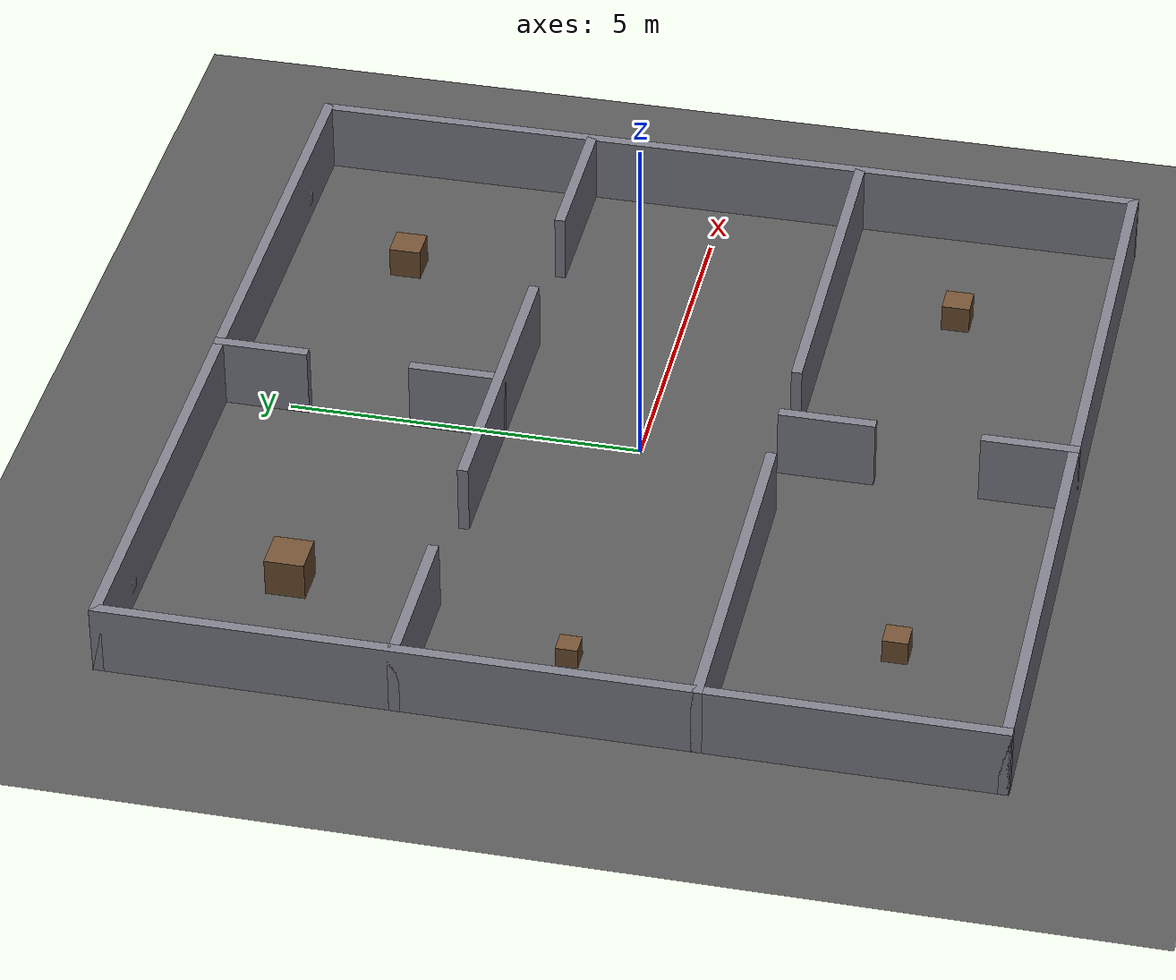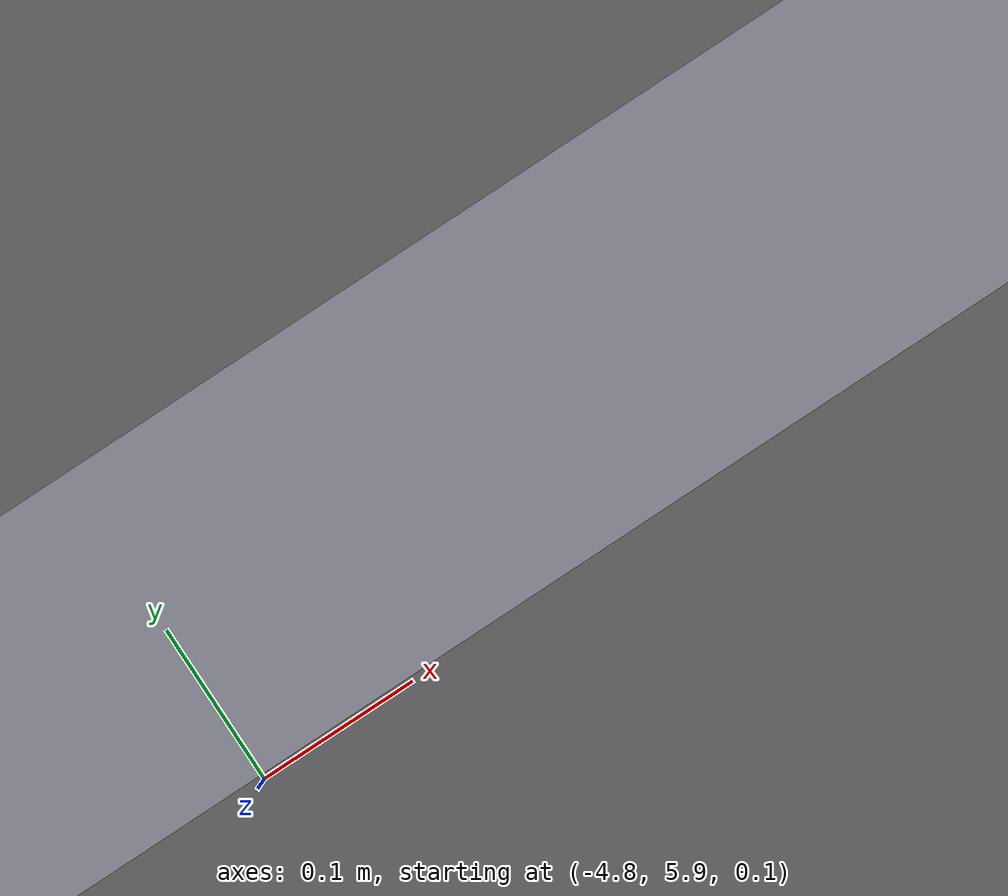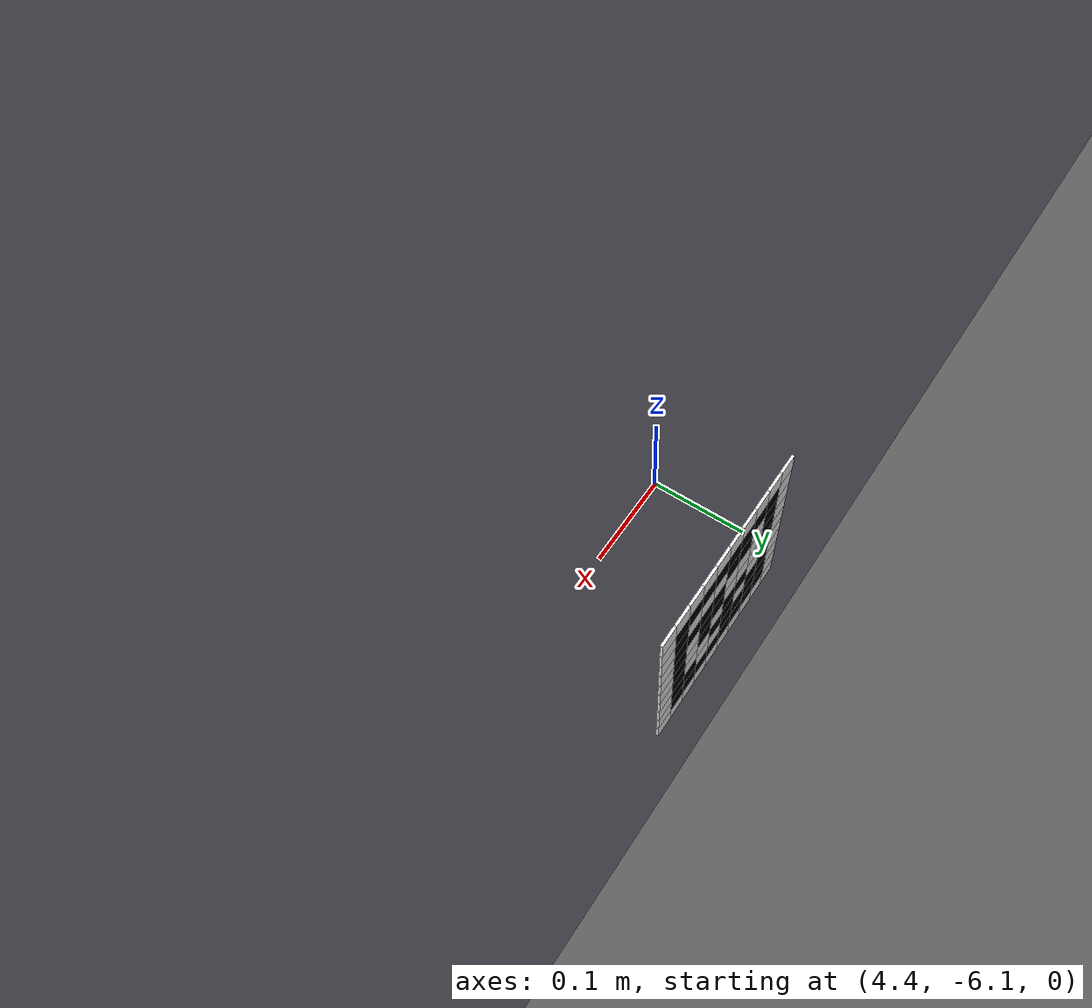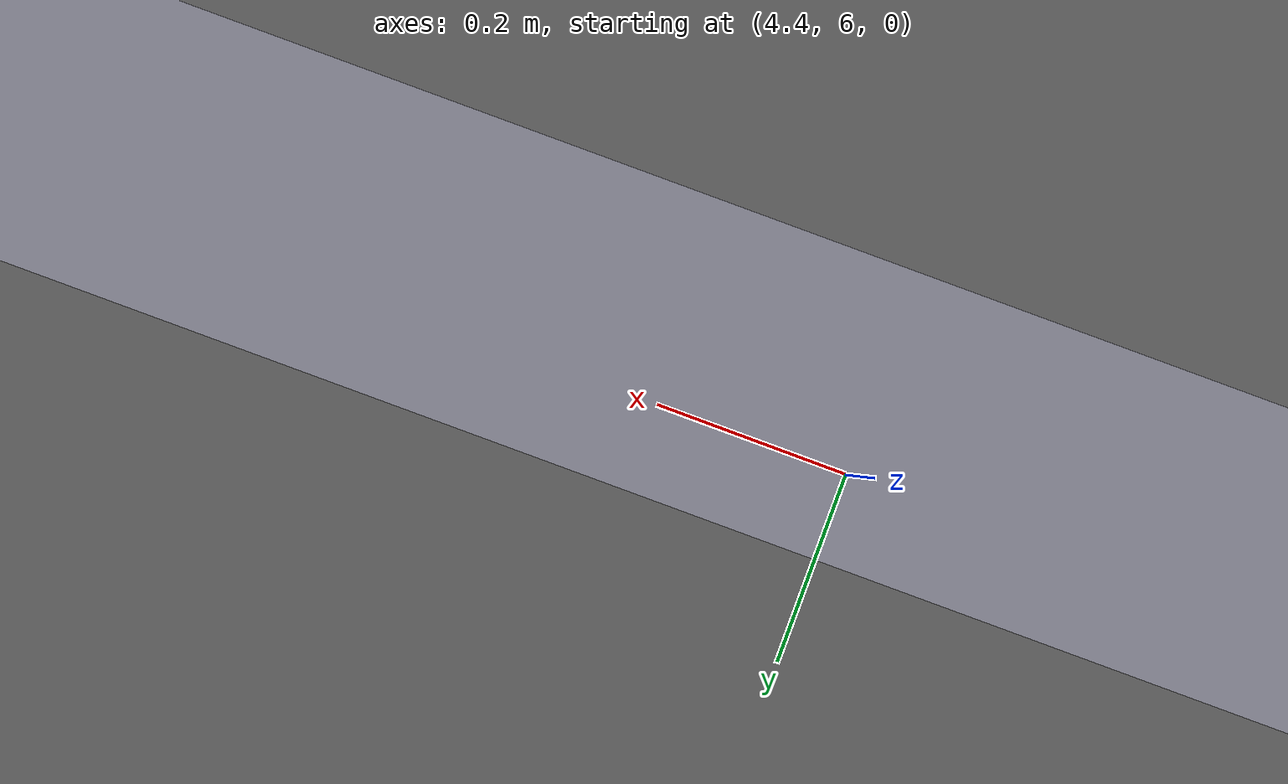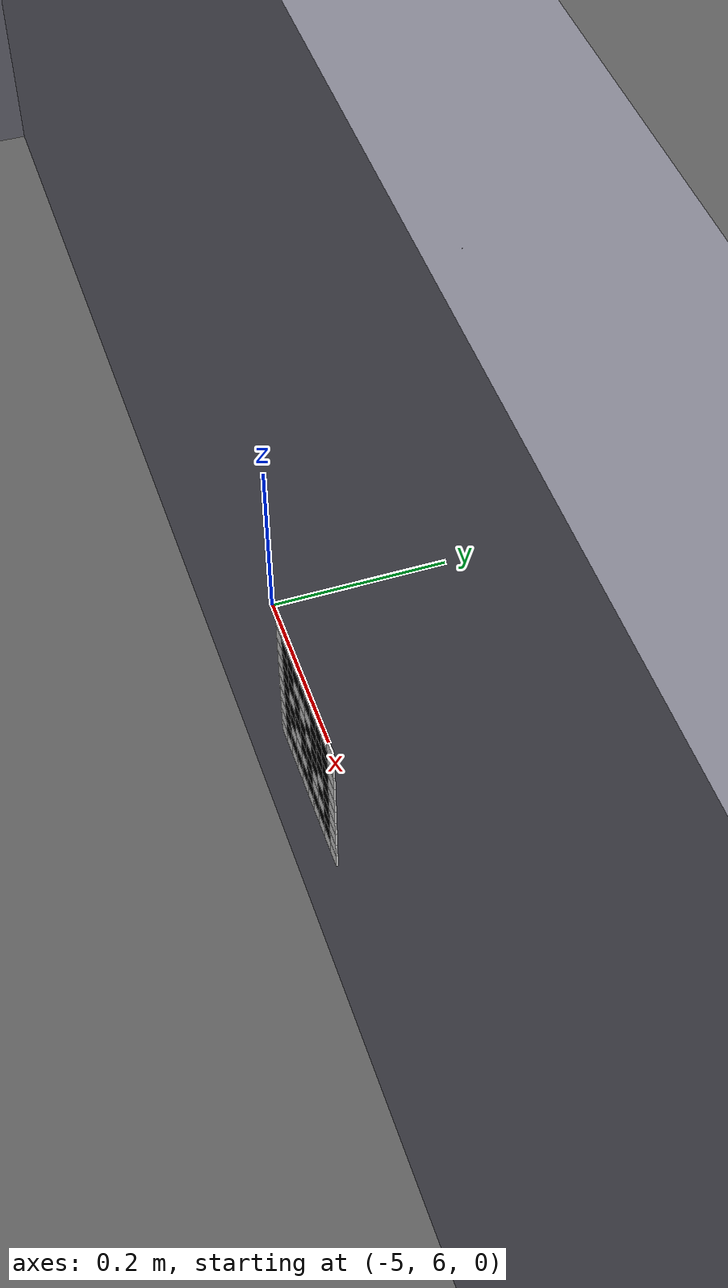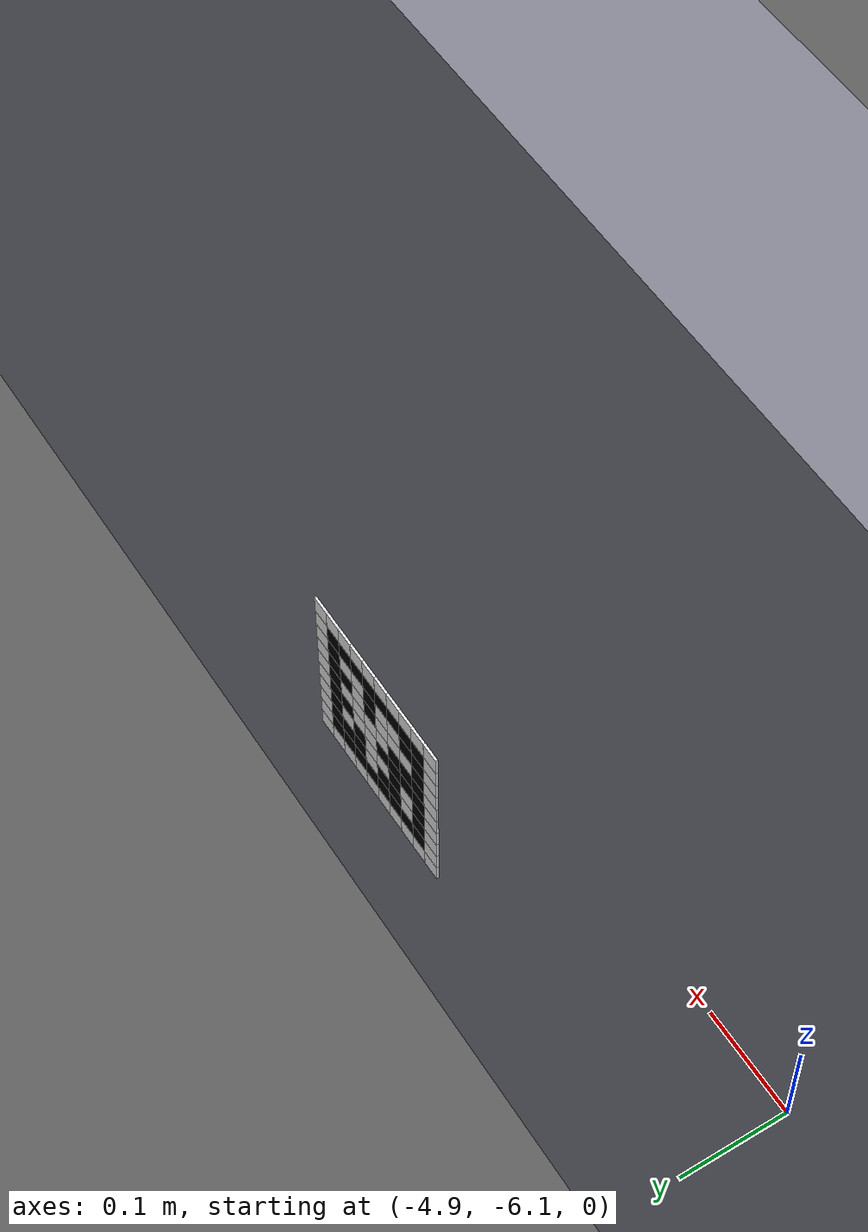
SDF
<?xml version="1.0"?>
<!-- Auto-generated by scripts/generate_rescue_arena.py — do not edit by hand. -->
<sdf version='1.8'>
    <world name='rescue_arena'>
        <physics name='1ms' type='ignored'>
            <max_step_size>0.01</max_step_size>
            <real_time_factor>1</real_time_factor>
            <real_time_update_rate>70</real_time_update_rate>
        </physics>
        <plugin name='ignition::gazebo::systems::Physics' filename='ignition-gazebo-physics-system' />
        <plugin name='ignition::gazebo::systems::UserCommands' filename='ignition-gazebo-user-commands-system' />
        <plugin name='ignition::gazebo::systems::SceneBroadcaster' filename='ignition-gazebo-scene-broadcaster-system' />
        <plugin name='ignition::gazebo::systems::Contact' filename='ignition-gazebo-contact-system' />
        <light name='sun' type='directional'>
            <cast_shadows>0</cast_shadows>
            <pose>0 0 10 0 0 0</pose>
            <diffuse>0.9 0.9 0.9 1</diffuse>
            <specular>0.1 0.1 0.1 1</specular>
            <attenuation><range>1000</range><constant>0.9</constant><linear>0.01</linear><quadratic>0.001</quadratic></attenuation>
            <direction>-0.4 0.2 -0.9</direction>
        </light>
        <gravity>0 0 -9.8</gravity>
        <scene>
            <ambient>0.5 0.5 0.5 1</ambient>
            <background>0.7 0.7 0.75 1</background>
            <shadows>0</shadows>
        </scene>
        <model name='ground_plane'>
            <static>1</static>
            <link name='link'>
                <collision name='collision'>
                    <geometry><plane><normal>0 0 1</normal><size>100 100</size></plane></geometry>
                </collision>
                <visual name='visual'>
                    <geometry><plane><normal>0 0 1</normal><size>100 100</size></plane></geometry>
                    <material><ambient>0.3 0.3 0.3 1</ambient><diffuse>0.35 0.35 0.35 1</diffuse></material>
                </visual>
            </link>
        </model>
        <model name='wall_0'>
            <static>1</static>
            <pose>0.000 6.000 0.500 0 0 0</pose>
            <link name='link'>
                <collision name='collision'>
                    <geometry><box><size>12.150 0.150 1.000</size></box></geometry>
                </collision>
                <visual name='visual'>
                    <geometry><box><size>12.150 0.150 1.000</size></box></geometry>
                    <material>
                        <ambient>0.5 0.5 0.55 1</ambient><diffuse>0.5 0.5 0.55 1</diffuse>
                    </material>
                </visual>
            </link>
        </model>
        <model name='wall_1'>
            <static>1</static>
            <pose>0.000 -6.000 0.500 0 0 0</pose>
            <link name='link'>
                <collision name='collision'>
                    <geometry><box><size>12.150 0.150 1.000</size></box></geometry>
                </collision>
                <visual name='visual'>
                    <geometry><box><size>12.150 0.150 1.000</size></box></geometry>
                    <material>
                        <ambient>0.5 0.5 0.55 1</ambient><diffuse>0.5 0.5 0.55 1</diffuse>
                    </material>
                </visual>
            </link>
        </model>
        <model name='wall_2'>
            <static>1</static>
            <pose>6.000 0.000 0.500 0 0 0</pose>
            <link name='link'>
                <collision name='collision'>
                    <geometry><box><size>0.150 12.150 1.000</size></box></geometry>
                </collision>
                <visual name='visual'>
                    <geometry><box><size>0.150 12.150 1.000</size></box></geometry>
                    <material>
                        <ambient>0.5 0.5 0.55 1</ambient><diffuse>0.5 0.5 0.55 1</diffuse>
                    </material>
                </visual>
            </link>
        </model>
        <model name='wall_3'>
            <static>1</static>
            <pose>-6.000 0.000 0.500 0 0 0</pose>
            <link name='link'>
                <collision name='collision'>
                    <geometry><box><size>0.150 12.150 1.000</size></box></geometry>
                </collision>
                <visual name='visual'>
                    <geometry><box><size>0.150 12.150 1.000</size></box></geometry>
                    <material>
                        <ambient>0.5 0.5 0.55 1</ambient><diffuse>0.5 0.5 0.55 1</diffuse>
                    </material>
                </visual>
            </link>
        </model>
        <model name='wall_4'>
            <static>1</static>
            <pose>-4.950 2.000 0.500 0 0 0</pose>
            <link name='link'>
                <collision name='collision'>
                    <geometry><box><size>2.250 0.150 1.000</size></box></geometry>
                </collision>
                <visual name='visual'>
                    <geometry><box><size>2.250 0.150 1.000</size></box></geometry>
                    <material>
                        <ambient>0.5 0.5 0.55 1</ambient><diffuse>0.5 0.5 0.55 1</diffuse>
                    </material>
                </visual>
            </link>
        </model>
        <model name='wall_5'>
            <static>1</static>
            <pose>0.000 2.000 0.500 0 0 0</pose>
            <link name='link'>
                <collision name='collision'>
                    <geometry><box><size>4.350 0.150 1.000</size></box></geometry>
                </collision>
                <visual name='visual'>
                    <geometry><box><size>4.350 0.150 1.000</size></box></geometry>
                    <material>
                        <ambient>0.5 0.5 0.55 1</ambient><diffuse>0.5 0.5 0.55 1</diffuse>
                    </material>
                </visual>
            </link>
        </model>
        <model name='wall_6'>
            <static>1</static>
            <pose>4.950 2.000 0.500 0 0 0</pose>
            <link name='link'>
                <collision name='collision'>
                    <geometry><box><size>2.250 0.150 1.000</size></box></geometry>
                </collision>
                <visual name='visual'>
                    <geometry><box><size>2.250 0.150 1.000</size></box></geometry>
                    <material>
                        <ambient>0.5 0.5 0.55 1</ambient><diffuse>0.5 0.5 0.55 1</diffuse>
                    </material>
                </visual>
            </link>
        </model>
        <model name='wall_7'>
            <static>1</static>
            <pose>-3.500 -2.000 0.500 0 0 0</pose>
            <link name='link'>
                <collision name='collision'>
                    <geometry><box><size>5.150 0.150 1.000</size></box></geometry>
                </collision>
                <visual name='visual'>
                    <geometry><box><size>5.150 0.150 1.000</size></box></geometry>
                    <material>
                        <ambient>0.5 0.5 0.55 1</ambient><diffuse>0.5 0.5 0.55 1</diffuse>
                    </material>
                </visual>
            </link>
        </model>
        <model name='wall_8'>
            <static>1</static>
            <pose>3.500 -2.000 0.500 0 0 0</pose>
            <link name='link'>
                <collision name='collision'>
                    <geometry><box><size>5.150 0.150 1.000</size></box></geometry>
                </collision>
                <visual name='visual'>
                    <geometry><box><size>5.150 0.150 1.000</size></box></geometry>
                    <material>
                        <ambient>0.5 0.5 0.55 1</ambient><diffuse>0.5 0.5 0.55 1</diffuse>
                    </material>
                </visual>
            </link>
        </model>
        <model name='wall_9'>
            <static>1</static>
            <pose>0.000 2.600 0.500 0 0 0</pose>
            <link name='link'>
                <collision name='collision'>
                    <geometry><box><size>0.150 1.350 1.000</size></box></geometry>
                </collision>
                <visual name='visual'>
                    <geometry><box><size>0.150 1.350 1.000</size></box></geometry>
                    <material>
                        <ambient>0.5 0.5 0.55 1</ambient><diffuse>0.5 0.5 0.55 1</diffuse>
                    </material>
                </visual>
            </link>
        </model>
        <model name='wall_10'>
            <static>1</static>
            <pose>0.000 5.400 0.500 0 0 0</pose>
            <link name='link'>
                <collision name='collision'>
                    <geometry><box><size>0.150 1.350 1.000</size></box></geometry>
                </collision>
                <visual name='visual'>
                    <geometry><box><size>0.150 1.350 1.000</size></box></geometry>
                    <material>
                        <ambient>0.5 0.5 0.55 1</ambient><diffuse>0.5 0.5 0.55 1</diffuse>
                    </material>
                </visual>
            </link>
        </model>
        <model name='wall_11'>
            <static>1</static>
            <pose>0.000 -5.400 0.500 0 0 0</pose>
            <link name='link'>
                <collision name='collision'>
                    <geometry><box><size>0.150 1.350 1.000</size></box></geometry>
                </collision>
                <visual name='visual'>
                    <geometry><box><size>0.150 1.350 1.000</size></box></geometry>
                    <material>
                        <ambient>0.5 0.5 0.55 1</ambient><diffuse>0.5 0.5 0.55 1</diffuse>
                    </material>
                </visual>
            </link>
        </model>
        <model name='wall_12'>
            <static>1</static>
            <pose>0.000 -2.600 0.500 0 0 0</pose>
            <link name='link'>
                <collision name='collision'>
                    <geometry><box><size>0.150 1.350 1.000</size></box></geometry>
                </collision>
                <visual name='visual'>
                    <geometry><box><size>0.150 1.350 1.000</size></box></geometry>
                    <material>
                        <ambient>0.5 0.5 0.55 1</ambient><diffuse>0.5 0.5 0.55 1</diffuse>
                    </material>
                </visual>
            </link>
        </model>
        <model name='rubble_0'>
            <static>1</static>
            <pose>3.600 4.200 0.225 0 0 0</pose>
            <link name='link'>
                <collision name='collision'>
                    <geometry><box><size>0.450 0.450 0.450</size></box></geometry>
                </collision>
                <visual name='visual'>
                    <geometry><box><size>0.450 0.450 0.450</size></box></geometry>
                    <material>
                        <ambient>0.45 0.32 0.2 1</ambient><diffuse>0.45 0.32 0.2 1</diffuse>
                    </material>
                </visual>
            </link>
        </model>
        <model name='rubble_1'>
            <static>1</static>
            <pose>-3.800 4.000 0.275 0 0 0</pose>
            <link name='link'>
                <collision name='collision'>
                    <geometry><box><size>0.550 0.550 0.550</size></box></geometry>
                </collision>
                <visual name='visual'>
                    <geometry><box><size>0.550 0.550 0.550</size></box></geometry>
                    <material>
                        <ambient>0.45 0.32 0.2 1</ambient><diffuse>0.45 0.32 0.2 1</diffuse>
                    </material>
                </visual>
            </link>
        </model>
        <model name='rubble_2'>
            <static>1</static>
            <pose>-3.600 -4.200 0.175 0 0 0</pose>
            <link name='link'>
                <collision name='collision'>
                    <geometry><box><size>0.350 0.350 0.350</size></box></geometry>
                </collision>
                <visual name='visual'>
                    <geometry><box><size>0.350 0.350 0.350</size></box></geometry>
                    <material>
                        <ambient>0.45 0.32 0.2 1</ambient><diffuse>0.45 0.32 0.2 1</diffuse>
                    </material>
                </visual>
            </link>
        </model>
        <model name='rubble_3'>
            <static>1</static>
            <pose>3.900 -3.800 0.200 0 0 0</pose>
            <link name='link'>
                <collision name='collision'>
                    <geometry><box><size>0.400 0.400 0.400</size></box></geometry>
                </collision>
                <visual name='visual'>
                    <geometry><box><size>0.400 0.400 0.400</size></box></geometry>
                    <material>
                        <ambient>0.45 0.32 0.2 1</ambient><diffuse>0.45 0.32 0.2 1</diffuse>
                    </material>
                </visual>
            </link>
        </model>
        <model name='rubble_4'>
            <static>1</static>
            <pose>-4.600 0.000 0.150 0 0 0</pose>
            <link name='link'>
                <collision name='collision'>
                    <geometry><box><size>0.300 0.300 0.300</size></box></geometry>
                </collision>
                <visual name='visual'>
                    <geometry><box><size>0.300 0.300 0.300</size></box></geometry>
                    <material>
                        <ambient>0.45 0.32 0.2 1</ambient><diffuse>0.45 0.32 0.2 1</diffuse>
                    </material>
                </visual>
            </link>
        </model>
        <!-- AprilTag victims (one per room) -->
        <include>
            <uri>model://apriltag_36h11_00</uri>
            <name>victim_0</name>
            <pose>4.6000 5.9240 0.2800 1.5708 0.0000 0.0000</pose>
        </include>
        <include>
            <uri>model://apriltag_36h11_01</uri>
            <name>victim_1</name>
            <pose>-4.6000 -5.9240 0.2800 -1.5708 0.0000 0.0000</pose>
        </include>
        <include>
            <uri>model://apriltag_36h11_02</uri>
            <name>victim_2</name>
            <pose>-4.6000 5.9240 0.2800 1.5708 0.0000 0.0000</pose>
        </include>
        <include>
            <uri>model://apriltag_36h11_03</uri>
            <name>victim_3</name>
            <pose>4.6000 -5.9240 0.2800 -1.5708 0.0000 0.0000</pose>
        </include>
    </world>
</sdf>

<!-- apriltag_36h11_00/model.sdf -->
<sdf version="1.8">
  <model name="apriltag_36h11_00">
    <static>true</static>
    <link name="link">
      <visual name="c0000">
        <pose>-0.072000 0.072000 0 0 0 0</pose>
        <geometry><box><size>0.015950 0.015950 0.002</size></box></geometry>
        <material>
          <ambient>1 1 1 1</ambient>
          <diffuse>1 1 1 1</diffuse>
          <specular>0 0 0 1</specular>
        </material>
      </visual>
      <visual name="c0001">
        <pose>-0.056000 0.072000 0 0 0 0</pose>
        <geometry><box><size>0.015950 0.015950 0.002</size></box></geometry>
        <material>
          <ambient>1 1 1 1</ambient>
          <diffuse>1 1 1 1</diffuse>
          <specular>0 0 0 1</specular>
        </material>
      </visual>
      <visual name="c0002">
        <pose>-0.040000 0.072000 0 0 0 0</pose>
        <geometry><box><size>0.015950 0.015950 0.002</size></box></geometry>
        <material>
          <ambient>1 1 1 1</ambient>
          <diffuse>1 1 1 1</diffuse>
          <specular>0 0 0 1</specular>
        </material>
      </visual>
      <visual name="c0003">
        <pose>-0.024000 0.072000 0 0 0 0</pose>
        <geometry><box><size>0.015950 0.015950 0.002</size></box></geometry>
        <material>
          <ambient>1 1 1 1</ambient>
          <diffuse>1 1 1 1</diffuse>
          <specular>0 0 0 1</specular>
        </material>
      </visual>
      <visual name="c0004">
        <pose>-0.008000 0.072000 0 0 0 0</pose>
        <geometry><box><size>0.015950 0.015950 0.002</size></box></geometry>
        <material>
          <ambient>1 1 1 1</ambient>
          <diffuse>1 1 1 1</diffuse>
          <specular>0 0 0 1</specular>
        </material>
      </visual>
      <visual name="c0005">
        <pose>0.008000 0.072000 0 0 0 0</pose>
        <geometry><box><size>0.015950 0.015950 0.002</size></box></geometry>
        <material>
          <ambient>1 1 1 1</ambient>
          <diffuse>1 1 1 1</diffuse>
          <specular>0 0 0 1</specular>
        </material>
      </visual>
      <visual name="c0006">
        <pose>0.024000 0.072000 0 0 0 0</pose>
        <geometry><box><size>0.015950 0.015950 0.002</size></box></geometry>
        <material>
          <ambient>1 1 1 1</ambient>
          <diffuse>1 1 1 1</diffuse>
          <specular>0 0 0 1</specular>
        </material>
      </visual>
      <visual name="c0007">
        <pose>0.040000 0.072000 0 0 0 0</pose>
        <geometry><box><size>0.015950 0.015950 0.002</size></box></geometry>
        <material>
          <ambient>1 1 1 1</ambient>
          <diffuse>1 1 1 1</diffuse>
          <specular>0 0 0 1</specular>
        </material>
      </visual>
      <visual name="c0008">
        <pose>0.056000 0.072000 0 0 0 0</pose>
        <geometry><box><size>0.015950 0.015950 0.002</size></box></geometry>
        <material>
          <ambient>1 1 1 1</ambient>
          <diffuse>1 1 1 1</diffuse>
          <specular>0 0 0 1</specular>
        </material>
      </visual>
      <visual name="c0009">
        <pose>0.072000 0.072000 0 0 0 0</pose>
        <geometry><box><size>0.015950 0.015950 0.002</size></box></geometry>
        <material>
          <ambient>1 1 1 1</ambient>
          <diffuse>1 1 1 1</diffuse>
          <specular>0 0 0 1</specular>
        </material>
      </visual>
      <visual name="c0100">
        <pose>-0.072000 0.056000 0 0 0 0</pose>
        <geometry><box><size>0.015950 0.015950 0.002</size></box></geometry>
        <material>
          <ambient>1 1 1 1</ambient>
          <diffuse>1 1 1 1</diffuse>
          <specular>0 0 0 1</specular>
        </material>
      </visual>
      <visual name="c0101">
        <pose>-0.056000 0.056000 0 0 0 0</pose>
        <geometry><box><size>0.015950 0.015950 0.002</size></box></geometry>
        <material>
          <ambient>0 0 0 1</ambient>
          <diffuse>0 0 0 1</diffuse>
          <specular>0 0 0 1</specular>
        </material>
      </visual>
      <visual name="c0102">
        <pose>-0.040000 0.056000 0 0 0 0</pose>
        <geometry><box><size>0.015950 0.015950 0.002</size></box></geometry>
        <material>
          <ambient>0 0 0 1</ambient>
          <diffuse>0 0 0 1</diffuse>
          <specular>0 0 0 1</specular>
        </material>
      </visual>
      <visual name="c0103">
        <pose>-0.024000 0.056000 0 0 0 0</pose>
        <geometry><box><size>0.015950 0.015950 0.002</size></box></geometry>
        <material>
          <ambient>0 0 0 1</ambient>
          <diffuse>0 0 0 1</diffuse>
          <specular>0 0 0 1</specular>
        </material>
      </visual>
      <visual name="c0104">
        <pose>-0.008000 0.056000 0 0 0 0</pose>
        <geometry><box><size>0.015950 0.015950 0.002</size></box></geometry>
        <material>
          <ambient>0 0 0 1</ambient>
          <diffuse>0 0 0 1</diffuse>
          <specular>0 0 0 1</specular>
        </material>
      </visual>
      <visual name="c0105">
        <pose>0.008000 0.056000 0 0 0 0</pose>
        <geometry><box><size>0.015950 0.015950 0.002</size></box></geometry>
        <material>
          <ambient>0 0 0 1</ambient>
          <diffuse>0 0 0 1</diffuse>
          <specular>0 0 0 1</specular>
        </material>
      </visual>
      <visual name="c0106">
        <pose>0.024000 0.056000 0 0 0 0</pose>
        <geometry><box><size>0.015950 0.015950 0.002</size></box></geometry>
        <material>
          <ambient>0 0 0 1</ambient>
          <diffuse>0 0 0 1</diffuse>
          <specular>0 0 0 1</specular>
        </material>
      </visual>
      <visual name="c0107">
        <pose>0.040000 0.056000 0 0 0 0</pose>
        <geometry><box><size>0.015950 0.015950 0.002</size></box></geometry>
        <material>
          <ambient>0 0 0 1</ambient>
          <diffuse>0 0 0 1</diffuse>
          <specular>0 0 0 1</specular>
        </material>
      </visual>
      <visual name="c0108">
        <pose>0.056000 0.056000 0 0 0 0</pose>
        <geometry><box><size>0.015950 0.015950 0.002</size></box></geometry>
        <material>
          <ambient>0 0 0 1</ambient>
          <diffuse>0 0 0 1</diffuse>
          <specular>0 0 0 1</specular>
        </material>
      </visual>
      <visual name="c0109">
        <pose>0.072000 0.056000 0 0 0 0</pose>
        <geometry><box><size>0.015950 0.015950 0.002</size></box></geometry>
        <material>
          <ambient>1 1 1 1</ambient>
          <diffuse>1 1 1 1</diffuse>
          <specular>0 0 0 1</specular>
        </material>
      </visual>
      <visual name="c0200">
        <pose>-0.072000 0.040000 0 0 0 0</pose>
        <geometry><box><size>0.015950 0.015950 0.002</size></box></geometry>
        <material>
          <ambient>1 1 1 1</ambient>
          <diffuse>1 1 1 1</diffuse>
          <specular>0 0 0 1</specular>
        </material>
      </visual>
      <visual name="c0201">
        <pose>-0.056000 0.040000 0 0 0 0</pose>
        <geometry><box><size>0.015950 0.015950 0.002</size></box></geometry>
        <material>
          <ambient>0 0 0 1</ambient>
          <diffuse>0 0 0 1</diffuse>
          <specular>0 0 0 1</specular>
        </material>
      </visual>
      <visual name="c0202">
        <pose>-0.040000 0.040000 0 0 0 0</pose>
        <geometry><box><size>0.015950 0.015950 0.002</size></box></geometry>
        <material>
          <ambient>0 0 0 1</ambient>
          <diffuse>0 0 0 1</diffuse>
          <specular>0 0 0 1</specular>
        </material>
      </visual>
      <visual name="c0203">
        <pose>-0.024000 0.040000 0 0 0 0</pose>
        <geometry><box><size>0.015950 0.015950 0.002</size></box></geometry>
        <material>
          <ambient>0 0 0 1</ambient>
          <diffuse>0 0 0 1</diffuse>
          <specular>0 0 0 1</specular>
        </material>
      </visual>
      <visual name="c0204">
        <pose>-0.008000 0.040000 0 0 0 0</pose>
        <geometry><box><size>0.015950 0.015950 0.002</size></box></geometry>
        <material>
          <ambient>1 1 1 1</ambient>
          <diffuse>1 1 1 1</diffuse>
          <specular>0 0 0 1</specular>
        </material>
      </visual>
      <visual name="c0205">
        <pose>0.008000 0.040000 0 0 0 0</pose>
        <geometry><box><size>0.015950 0.015950 0.002</size></box></geometry>
        <material>
          <ambient>0 0 0 1</ambient>
          <diffuse>0 0 0 1</diffuse>
          <specular>0 0 0 1</specular>
        </material>
      </visual>
      <visual name="c0206">
        <pose>0.024000 0.040000 0 0 0 0</pose>
        <geometry><box><size>0.015950 0.015950 0.002</size></box></geometry>
        <material>
          <ambient>0 0 0 1</ambient>
          <diffuse>0 0 0 1</diffuse>
          <specular>0 0 0 1</specular>
        </material>
      </visual>
      <visual name="c0207">
        <pose>0.040000 0.040000 0 0 0 0</pose>
        <geometry><box><size>0.015950 0.015950 0.002</size></box></geometry>
        <material>
          <ambient>0 0 0 1</ambient>
          <diffuse>0 0 0 1</diffuse>
          <specular>0 0 0 1</specular>
        </material>
      </visual>
      <visual name="c0208">
        <pose>0.056000 0.040000 0 0 0 0</pose>
        <geometry><box><size>0.015950 0.015950 0.002</size></box></geometry>
        <material>
          <ambient>0 0 0 1</ambient>
          <diffuse>0 0 0 1</diffuse>
          <specular>0 0 0 1</specular>
        </material>
      </visual>
      <visual name="c0209">
        <pose>0.072000 0.040000 0 0 0 0</pose>
        <geometry><box><size>0.015950 0.015950 0.002</size></box></geometry>
        <material>
          <ambient>1 1 1 1</ambient>
          <diffuse>1 1 1 1</diffuse>
          <specular>0 0 0 1</specular>
        </material>
      </visual>
      <visual name="c0300">
        <pose>-0.072000 0.024000 0 0 0 0</pose>
        <geometry><box><size>0.015950 0.015950 0.002</size></box></geometry>
        <material>
          <ambient>1 1 1 1</ambient>
          <diffuse>1 1 1 1</diffuse>
          <specular>0 0 0 1</specular>
        </material>
      </visual>
      <visual name="c0301">
        <pose>-0.056000 0.024000 0 0 0 0</pose>
        <geometry><box><size>0.015950 0.015950 0.002</size></box></geometry>
        <material>
          <ambient>0 0 0 1</ambient>
          <diffuse>0 0 0 1</diffuse>
          <specular>0 0 0 1</specular>
        </material>
      </visual>
      <visual name="c0302">
        <pose>-0.040000 0.024000 0 0 0 0</pose>
        <geometry><box><size>0.015950 0.015950 0.002</size></box></geometry>
        <material>
          <ambient>0 0 0 1</ambient>
          <diffuse>0 0 0 1</diffuse>
          <specular>0 0 0 1</specular>
        </material>
      </visual>
      <visual name="c0303">
        <pose>-0.024000 0.024000 0 0 0 0</pose>
        <geometry><box><size>0.015950 0.015950 0.002</size></box></geometry>
        <material>
          <ambient>1 1 1 1</ambient>
          <diffuse>1 1 1 1</diffuse>
          <specular>0 0 0 1</specular>
        </material>
      </visual>
      <visual name="c0304">
        <pose>-0.008000 0.024000 0 0 0 0</pose>
        <geometry><box><size>0.015950 0.015950 0.002</size></box></geometry>
        <material>
          <ambient>1 1 1 1</ambient>
          <diffuse>1 1 1 1</diffuse>
          <specular>0 0 0 1</specular>
        </material>
      </visual>
      <visual name="c0305">
        <pose>0.008000 0.024000 0 0 0 0</pose>
        <geometry><box><size>0.015950 0.015950 0.002</size></box></geometry>
        <material>
          <ambient>0 0 0 1</ambient>
          <diffuse>0 0 0 1</diffuse>
          <specular>0 0 0 1</specular>
        </material>
      </visual>
      <visual name="c0306">
        <pose>0.024000 0.024000 0 0 0 0</pose>
        <geometry><box><size>0.015950 0.015950 0.002</size></box></geometry>
        <material>
          <ambient>1 1 1 1</ambient>
          <diffuse>1 1 1 1</diffuse>
          <specular>0 0 0 1</specular>
        </material>
      </visual>
      <visual name="c0307">
        <pose>0.040000 0.024000 0 0 0 0</pose>
        <geometry><box><size>0.015950 0.015950 0.002</size></box></geometry>
        <material>
          <ambient>0 0 0 1</ambient>
          <diffuse>0 0 0 1</diffuse>
          <specular>0 0 0 1</specular>
        </material>
      </visual>
      <visual name="c0308">
        <pose>0.056000 0.024000 0 0 0 0</pose>
        <geometry><box><size>0.015950 0.015950 0.002</size></box></geometry>
        <material>
          <ambient>0 0 0 1</ambient>
          <diffuse>0 0 0 1</diffuse>
          <specular>0 0 0 1</specular>
        </material>
      </visual>
      <visual name="c0309">
        <pose>0.072000 0.024000 0 0 0 0</pose>
        <geometry><box><size>0.015950 0.015950 0.002</size></box></geometry>
        <material>
          <ambient>1 1 1 1</ambient>
          <diffuse>1 1 1 1</diffuse>
          <specular>0 0 0 1</specular>
        </material>
      </visual>
      <visual name="c0400">
        <pose>-0.072000 0.008000 0 0 0 0</pose>
        <geometry><box><size>0.015950 0.015950 0.002</size></box></geometry>
        <material>
          <ambient>1 1 1 1</ambient>
          <diffuse>1 1 1 1</diffuse>
          <specular>0 0 0 1</specular>
        </material>
      </visual>
      <visual name="c0401">
        <pose>-0.056000 0.008000 0 0 0 0</pose>
        <geometry><box><size>0.015950 0.015950 0.002</size></box></geometry>
        <material>
          <ambient>0 0 0 1</ambient>
          <diffuse>0 0 0 1</diffuse>
          <specular>0 0 0 1</specular>
        </material>
      </visual>
      <visual name="c0402">
        <pose>-0.040000 0.008000 0 0 0 0</pose>
        <geometry><box><size>0.015950 0.015950 0.002</size></box></geometry>
        <material>
          <ambient>0 0 0 1</ambient>
          <diffuse>0 0 0 1</diffuse>
          <specular>0 0 0 1</specular>
        </material>
      </visual>
      <visual name="c0403">
        <pose>-0.024000 0.008000 0 0 0 0</pose>
        <geometry><box><size>0.015950 0.015950 0.002</size></box></geometry>
        <material>
          <ambient>0 0 0 1</ambient>
          <diffuse>0 0 0 1</diffuse>
          <specular>0 0 0 1</specular>
        </material>
      </visual>
      <visual name="c0404">
        <pose>-0.008000 0.008000 0 0 0 0</pose>
        <geometry><box><size>0.015950 0.015950 0.002</size></box></geometry>
        <material>
          <ambient>0 0 0 1</ambient>
          <diffuse>0 0 0 1</diffuse>
          <specular>0 0 0 1</specular>
        </material>
      </visual>
      <visual name="c0405">
        <pose>0.008000 0.008000 0 0 0 0</pose>
        <geometry><box><size>0.015950 0.015950 0.002</size></box></geometry>
        <material>
          <ambient>1 1 1 1</ambient>
          <diffuse>1 1 1 1</diffuse>
          <specular>0 0 0 1</specular>
        </material>
      </visual>
      <visual name="c0406">
        <pose>0.024000 0.008000 0 0 0 0</pose>
        <geometry><box><size>0.015950 0.015950 0.002</size></box></geometry>
        <material>
          <ambient>0 0 0 1</ambient>
          <diffuse>0 0 0 1</diffuse>
          <specular>0 0 0 1</specular>
        </material>
      </visual>
      <visual name="c0407">
        <pose>0.040000 0.008000 0 0 0 0</pose>
        <geometry><box><size>0.015950 0.015950 0.002</size></box></geometry>
        <material>
          <ambient>1 1 1 1</ambient>
          <diffuse>1 1 1 1</diffuse>
          <specular>0 0 0 1</specular>
        </material>
      </visual>
      <visual name="c0408">
        <pose>0.056000 0.008000 0 0 0 0</pose>
        <geometry><box><size>0.015950 0.015950 0.002</size></box></geometry>
        <material>
          <ambient>0 0 0 1</ambient>
          <diffuse>0 0 0 1</diffuse>
          <specular>0 0 0 1</specular>
        </material>
      </visual>
      <visual name="c0409">
        <pose>0.072000 0.008000 0 0 0 0</pose>
        <geometry><box><size>0.015950 0.015950 0.002</size></box></geometry>
        <material>
          <ambient>1 1 1 1</ambient>
          <diffuse>1 1 1 1</diffuse>
          <specular>0 0 0 1</specular>
        </material>
      </visual>
      <visual name="c0500">
        <pose>-0.072000 -0.008000 0 0 0 0</pose>
        <geometry><box><size>0.015950 0.015950 0.002</size></box></geometry>
        <material>
          <ambient>1 1 1 1</ambient>
          <diffuse>1 1 1 1</diffuse>
          <specular>0 0 0 1</specular>
        </material>
      </visual>
      <visual name="c0501">
        <pose>-0.056000 -0.008000 0 0 0 0</pose>
        <geometry><box><size>0.015950 0.015950 0.002</size></box></geometry>
        <material>
          <ambient>0 0 0 1</ambient>
          <diffuse>0 0 0 1</diffuse>
          <specular>0 0 0 1</specular>
        </material>
      </visual>
      <visual name="c0502">
        <pose>-0.040000 -0.008000 0 0 0 0</pose>
        <geometry><box><size>0.015950 0.015950 0.002</size></box></geometry>
        <material>
          <ambient>0 0 0 1</ambient>
          <diffuse>0 0 0 1</diffuse>
          <specular>0 0 0 1</specular>
        </material>
      </visual>
      <visual name="c0503">
        <pose>-0.024000 -0.008000 0 0 0 0</pose>
        <geometry><box><size>0.015950 0.015950 0.002</size></box></geometry>
        <material>
          <ambient>0 0 0 1</ambient>
          <diffuse>0 0 0 1</diffuse>
          <specular>0 0 0 1</specular>
        </material>
      </visual>
      <visual name="c0504">
        <pose>-0.008000 -0.008000 0 0 0 0</pose>
        <geometry><box><size>0.015950 0.015950 0.002</size></box></geometry>
        <material>
          <ambient>0 0 0 1</ambient>
          <diffuse>0 0 0 1</diffuse>
          <specular>0 0 0 1</specular>
        </material>
      </visual>
      <visual name="c0505">
        <pose>0.008000 -0.008000 0 0 0 0</pose>
        <geometry><box><size>0.015950 0.015950 0.002</size></box></geometry>
        <material>
          <ambient>1 1 1 1</ambient>
          <diffuse>1 1 1 1</diffuse>
          <specular>0 0 0 1</specular>
        </material>
      </visual>
      <visual name="c0506">
        <pose>0.024000 -0.008000 0 0 0 0</pose>
        <geometry><box><size>0.015950 0.015950 0.002</size></box></geometry>
        <material>
          <ambient>1 1 1 1</ambient>
          <diffuse>1 1 1 1</diffuse>
          <specular>0 0 0 1</specular>
        </material>
      </visual>
      <visual name="c0507">
        <pose>0.040000 -0.008000 0 0 0 0</pose>
        <geometry><box><size>0.015950 0.015950 0.002</size></box></geometry>
        <material>
          <ambient>0 0 0 1</ambient>
          <diffuse>0 0 0 1</diffuse>
          <specular>0 0 0 1</specular>
        </material>
      </visual>
      <visual name="c0508">
        <pose>0.056000 -0.008000 0 0 0 0</pose>
        <geometry><box><size>0.015950 0.015950 0.002</size></box></geometry>
        <material>
          <ambient>0 0 0 1</ambient>
          <diffuse>0 0 0 1</diffuse>
          <specular>0 0 0 1</specular>
        </material>
      </visual>
      <visual name="c0509">
        <pose>0.072000 -0.008000 0 0 0 0</pose>
        <geometry><box><size>0.015950 0.015950 0.002</size></box></geometry>
        <material>
          <ambient>1 1 1 1</ambient>
          <diffuse>1 1 1 1</diffuse>
          <specular>0 0 0 1</specular>
        </material>
      </visual>
      <visual name="c0600">
        <pose>-0.072000 -0.024000 0 0 0 0</pose>
        <geometry><box><size>0.015950 0.015950 0.002</size></box></geometry>
        <material>
          <ambient>1 1 1 1</ambient>
          <diffuse>1 1 1 1</diffuse>
          <specular>0 0 0 1</specular>
        </material>
      </visual>
      <visual name="c0601">
        <pose>-0.056000 -0.024000 0 0 0 0</pose>
        <geometry><box><size>0.015950 0.015950 0.002</size></box></geometry>
        <material>
          <ambient>0 0 0 1</ambient>
          <diffuse>0 0 0 1</diffuse>
          <specular>0 0 0 1</specular>
        </material>
      </visual>
      <visual name="c0602">
        <pose>-0.040000 -0.024000 0 0 0 0</pose>
        <geometry><box><size>0.015950 0.015950 0.002</size></box></geometry>
        <material>
          <ambient>1 1 1 1</ambient>
          <diffuse>1 1 1 1</diffuse>
          <specular>0 0 0 1</specular>
        </material>
      </visual>
      <visual name="c0603">
        <pose>-0.024000 -0.024000 0 0 0 0</pose>
        <geometry><box><size>0.015950 0.015950 0.002</size></box></geometry>
        <material>
          <ambient>0 0 0 1</ambient>
          <diffuse>0 0 0 1</diffuse>
          <specular>0 0 0 1</specular>
        </material>
      </visual>
      <visual name="c0604">
        <pose>-0.008000 -0.024000 0 0 0 0</pose>
        <geometry><box><size>0.015950 0.015950 0.002</size></box></geometry>
        <material>
          <ambient>1 1 1 1</ambient>
          <diffuse>1 1 1 1</diffuse>
          <specular>0 0 0 1</specular>
        </material>
      </visual>
      <visual name="c0605">
        <pose>0.008000 -0.024000 0 0 0 0</pose>
        <geometry><box><size>0.015950 0.015950 0.002</size></box></geometry>
        <material>
          <ambient>1 1 1 1</ambient>
          <diffuse>1 1 1 1</diffuse>
          <specular>0 0 0 1</specular>
        </material>
      </visual>
      <visual name="c0606">
        <pose>0.024000 -0.024000 0 0 0 0</pose>
        <geometry><box><size>0.015950 0.015950 0.002</size></box></geometry>
        <material>
          <ambient>1 1 1 1</ambient>
          <diffuse>1 1 1 1</diffuse>
          <specular>0 0 0 1</specular>
        </material>
      </visual>
      <visual name="c0607">
        <pose>0.040000 -0.024000 0 0 0 0</pose>
        <geometry><box><size>0.015950 0.015950 0.002</size></box></geometry>
        <material>
          <ambient>0 0 0 1</ambient>
          <diffuse>0 0 0 1</diffuse>
          <specular>0 0 0 1</specular>
        </material>
      </visual>
      <visual name="c0608">
        <pose>0.056000 -0.024000 0 0 0 0</pose>
        <geometry><box><size>0.015950 0.015950 0.002</size></box></geometry>
        <material>
          <ambient>0 0 0 1</ambient>
          <diffuse>0 0 0 1</diffuse>
          <specular>0 0 0 1</specular>
        </material>
      </visual>
      <visual name="c0609">
        <pose>0.072000 -0.024000 0 0 0 0</pose>
        <geometry><box><size>0.015950 0.015950 0.002</size></box></geometry>
        <material>
          <ambient>1 1 1 1</ambient>
          <diffuse>1 1 1 1</diffuse>
          <specular>0 0 0 1</specular>
        </material>
      </visual>
      <visual name="c0700">
        <pose>-0.072000 -0.040000 0 0 0 0</pose>
        <geometry><box><size>0.015950 0.015950 0.002</size></box></geometry>
        <material>
          <ambient>1 1 1 1</ambient>
          <diffuse>1 1 1 1</diffuse>
          <specular>0 0 0 1</specular>
        </material>
      </visual>
      <visual name="c0701">
        <pose>-0.056000 -0.040000 0 0 0 0</pose>
        <geometry><box><size>0.015950 0.015950 0.002</size></box></geometry>
        <material>
          <ambient>0 0 0 1</ambient>
          <diffuse>0 0 0 1</diffuse>
          <specular>0 0 0 1</specular>
        </material>
      </visual>
      <visual name="c0702">
        <pose>-0.040000 -0.040000 0 0 0 0</pose>
        <geometry><box><size>0.015950 0.015950 0.002</size></box></geometry>
        <material>
          <ambient>1 1 1 1</ambient>
          <diffuse>1 1 1 1</diffuse>
          <specular>0 0 0 1</specular>
        </material>
      </visual>
      <visual name="c0703">
        <pose>-0.024000 -0.040000 0 0 0 0</pose>
        <geometry><box><size>0.015950 0.015950 0.002</size></box></geometry>
        <material>
          <ambient>0 0 0 1</ambient>
          <diffuse>0 0 0 1</diffuse>
          <specular>0 0 0 1</specular>
        </material>
      </visual>
      <visual name="c0704">
        <pose>-0.008000 -0.040000 0 0 0 0</pose>
        <geometry><box><size>0.015950 0.015950 0.002</size></box></geometry>
        <material>
          <ambient>1 1 1 1</ambient>
          <diffuse>1 1 1 1</diffuse>
          <specular>0 0 0 1</specular>
        </material>
      </visual>
      <visual name="c0705">
        <pose>0.008000 -0.040000 0 0 0 0</pose>
        <geometry><box><size>0.015950 0.015950 0.002</size></box></geometry>
        <material>
          <ambient>0 0 0 1</ambient>
          <diffuse>0 0 0 1</diffuse>
          <specular>0 0 0 1</specular>
        </material>
      </visual>
      <visual name="c0706">
        <pose>0.024000 -0.040000 0 0 0 0</pose>
        <geometry><box><size>0.015950 0.015950 0.002</size></box></geometry>
        <material>
          <ambient>1 1 1 1</ambient>
          <diffuse>1 1 1 1</diffuse>
          <specular>0 0 0 1</specular>
        </material>
      </visual>
      <visual name="c0707">
        <pose>0.040000 -0.040000 0 0 0 0</pose>
        <geometry><box><size>0.015950 0.015950 0.002</size></box></geometry>
        <material>
          <ambient>1 1 1 1</ambient>
          <diffuse>1 1 1 1</diffuse>
          <specular>0 0 0 1</specular>
        </material>
      </visual>
      <visual name="c0708">
        <pose>0.056000 -0.040000 0 0 0 0</pose>
        <geometry><box><size>0.015950 0.015950 0.002</size></box></geometry>
        <material>
          <ambient>0 0 0 1</ambient>
          <diffuse>0 0 0 1</diffuse>
          <specular>0 0 0 1</specular>
        </material>
      </visual>
      <visual name="c0709">
        <pose>0.072000 -0.040000 0 0 0 0</pose>
        <geometry><box><size>0.015950 0.015950 0.002</size></box></geometry>
        <material>
          <ambient>1 1 1 1</ambient>
          <diffuse>1 1 1 1</diffuse>
          <specular>0 0 0 1</specular>
        </material>
      </visual>
      <visual name="c0800">
        <pose>-0.072000 -0.056000 0 0 0 0</pose>
        <geometry><box><size>0.015950 0.015950 0.002</size></box></geometry>
        <material>
          <ambient>1 1 1 1</ambient>
          <diffuse>1 1 1 1</diffuse>
          <specular>0 0 0 1</specular>
        </material>
      </visual>
      <visual name="c0801">
        <pose>-0.056000 -0.056000 0 0 0 0</pose>
        <geometry><box><size>0.015950 0.015950 0.002</size></box></geometry>
        <material>
          <ambient>0 0 0 1</ambient>
          <diffuse>0 0 0 1</diffuse>
          <specular>0 0 0 1</specular>
        </material>
      </visual>
      <visual name="c0802">
        <pose>-0.040000 -0.056000 0 0 0 0</pose>
        <geometry><box><size>0.015950 0.015950 0.002</size></box></geometry>
        <material>
          <ambient>0 0 0 1</ambient>
          <diffuse>0 0 0 1</diffuse>
          <specular>0 0 0 1</specular>
        </material>
      </visual>
      <visual name="c0803">
        <pose>-0.024000 -0.056000 0 0 0 0</pose>
        <geometry><box><size>0.015950 0.015950 0.002</size></box></geometry>
        <material>
          <ambient>0 0 0 1</ambient>
          <diffuse>0 0 0 1</diffuse>
          <specular>0 0 0 1</specular>
        </material>
      </visual>
      <visual name="c0804">
        <pose>-0.008000 -0.056000 0 0 0 0</pose>
        <geometry><box><size>0.015950 0.015950 0.002</size></box></geometry>
        <material>
          <ambient>0 0 0 1</ambient>
          <diffuse>0 0 0 1</diffuse>
          <specular>0 0 0 1</specular>
        </material>
      </visual>
      <visual name="c0805">
        <pose>0.008000 -0.056000 0 0 0 0</pose>
        <geometry><box><size>0.015950 0.015950 0.002</size></box></geometry>
        <material>
          <ambient>0 0 0 1</ambient>
          <diffuse>0 0 0 1</diffuse>
          <specular>0 0 0 1</specular>
        </material>
      </visual>
      <visual name="c0806">
        <pose>0.024000 -0.056000 0 0 0 0</pose>
        <geometry><box><size>0.015950 0.015950 0.002</size></box></geometry>
        <material>
          <ambient>0 0 0 1</ambient>
          <diffuse>0 0 0 1</diffuse>
          <specular>0 0 0 1</specular>
        </material>
      </visual>
      <visual name="c0807">
        <pose>0.040000 -0.056000 0 0 0 0</pose>
        <geometry><box><size>0.015950 0.015950 0.002</size></box></geometry>
        <material>
          <ambient>0 0 0 1</ambient>
          <diffuse>0 0 0 1</diffuse>
          <specular>0 0 0 1</specular>
        </material>
      </visual>
      <visual name="c0808">
        <pose>0.056000 -0.056000 0 0 0 0</pose>
        <geometry><box><size>0.015950 0.015950 0.002</size></box></geometry>
        <material>
          <ambient>0 0 0 1</ambient>
          <diffuse>0 0 0 1</diffuse>
          <specular>0 0 0 1</specular>
        </material>
      </visual>
      <visual name="c0809">
        <pose>0.072000 -0.056000 0 0 0 0</pose>
        <geometry><box><size>0.015950 0.015950 0.002</size></box></geometry>
        <material>
          <ambient>1 1 1 1</ambient>
          <diffuse>1 1 1 1</diffuse>
          <specular>0 0 0 1</specular>
        </material>
      </visual>
      <visual name="c0900">
        <pose>-0.072000 -0.072000 0 0 0 0</pose>
        <geometry><box><size>0.015950 0.015950 0.002</size></box></geometry>
        <material>
          <ambient>1 1 1 1</ambient>
          <diffuse>1 1 1 1</diffuse>
          <specular>0 0 0 1</specular>
        </material>
      </visual>
      <visual name="c0901">
        <pose>-0.056000 -0.072000 0 0 0 0</pose>
        <geometry><box><size>0.015950 0.015950 0.002</size></box></geometry>
        <material>
          <ambient>1 1 1 1</ambient>
          <diffuse>1 1 1 1</diffuse>
          <specular>0 0 0 1</specular>
        </material>
      </visual>
      <visual name="c0902">
        <pose>-0.040000 -0.072000 0 0 0 0</pose>
        <geometry><box><size>0.015950 0.015950 0.002</size></box></geometry>
        <material>
          <ambient>1 1 1 1</ambient>
          <diffuse>1 1 1 1</diffuse>
          <specular>0 0 0 1</specular>
        </material>
      </visual>
      <visual name="c0903">
        <pose>-0.024000 -0.072000 0 0 0 0</pose>
        <geometry><box><size>0.015950 0.015950 0.002</size></box></geometry>
        <material>
          <ambient>1 1 1 1</ambient>
          <diffuse>1 1 1 1</diffuse>
          <specular>0 0 0 1</specular>
        </material>
      </visual>
      <visual name="c0904">
        <pose>-0.008000 -0.072000 0 0 0 0</pose>
        <geometry><box><size>0.015950 0.015950 0.002</size></box></geometry>
        <material>
          <ambient>1 1 1 1</ambient>
          <diffuse>1 1 1 1</diffuse>
          <specular>0 0 0 1</specular>
        </material>
      </visual>
      <visual name="c0905">
        <pose>0.008000 -0.072000 0 0 0 0</pose>
        <geometry><box><size>0.015950 0.015950 0.002</size></box></geometry>
        <material>
          <ambient>1 1 1 1</ambient>
          <diffuse>1 1 1 1</diffuse>
          <specular>0 0 0 1</specular>
        </material>
      </visual>
      <visual name="c0906">
        <pose>0.024000 -0.072000 0 0 0 0</pose>
        <geometry><box><size>0.015950 0.015950 0.002</size></box></geometry>
        <material>
          <ambient>1 1 1 1</ambient>
          <diffuse>1 1 1 1</diffuse>
          <specular>0 0 0 1</specular>
        </material>
      </visual>
      <visual name="c0907">
        <pose>0.040000 -0.072000 0 0 0 0</pose>
        <geometry><box><size>0.015950 0.015950 0.002</size></box></geometry>
        <material>
          <ambient>1 1 1 1</ambient>
          <diffuse>1 1 1 1</diffuse>
          <specular>0 0 0 1</specular>
        </material>
      </visual>
      <visual name="c0908">
        <pose>0.056000 -0.072000 0 0 0 0</pose>
        <geometry><box><size>0.015950 0.015950 0.002</size></box></geometry>
        <material>
          <ambient>1 1 1 1</ambient>
          <diffuse>1 1 1 1</diffuse>
          <specular>0 0 0 1</specular>
        </material>
      </visual>
      <visual name="c0909">
        <pose>0.072000 -0.072000 0 0 0 0</pose>
        <geometry><box><size>0.015950 0.015950 0.002</size></box></geometry>
        <material>
          <ambient>1 1 1 1</ambient>
          <diffuse>1 1 1 1</diffuse>
          <specular>0 0 0 1</specular>
        </material>
      </visual>
      <collision name="collision">
        <geometry>
          <box><size>0.16 0.16 0.003</size></box>
        </geometry>
      </collision>
    </link>
  </model>
</sdf>

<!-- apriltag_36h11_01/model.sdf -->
<sdf version="1.8">
  <model name="apriltag_36h11_01">
    <static>true</static>
    <link name="link">
      <visual name="c0000">
        <pose>-0.072000 0.072000 0 0 0 0</pose>
        <geometry><box><size>0.015950 0.015950 0.002</size></box></geometry>
        <material>
          <ambient>1 1 1 1</ambient>
          <diffuse>1 1 1 1</diffuse>
          <specular>0 0 0 1</specular>
        </material>
      </visual>
      <visual name="c0001">
        <pose>-0.056000 0.072000 0 0 0 0</pose>
        <geometry><box><size>0.015950 0.015950 0.002</size></box></geometry>
        <material>
          <ambient>1 1 1 1</ambient>
          <diffuse>1 1 1 1</diffuse>
          <specular>0 0 0 1</specular>
        </material>
      </visual>
      <visual name="c0002">
        <pose>-0.040000 0.072000 0 0 0 0</pose>
        <geometry><box><size>0.015950 0.015950 0.002</size></box></geometry>
        <material>
          <ambient>1 1 1 1</ambient>
          <diffuse>1 1 1 1</diffuse>
          <specular>0 0 0 1</specular>
        </material>
      </visual>
      <visual name="c0003">
        <pose>-0.024000 0.072000 0 0 0 0</pose>
        <geometry><box><size>0.015950 0.015950 0.002</size></box></geometry>
        <material>
          <ambient>1 1 1 1</ambient>
          <diffuse>1 1 1 1</diffuse>
          <specular>0 0 0 1</specular>
        </material>
      </visual>
      <visual name="c0004">
        <pose>-0.008000 0.072000 0 0 0 0</pose>
        <geometry><box><size>0.015950 0.015950 0.002</size></box></geometry>
        <material>
          <ambient>1 1 1 1</ambient>
          <diffuse>1 1 1 1</diffuse>
          <specular>0 0 0 1</specular>
        </material>
      </visual>
      <visual name="c0005">
        <pose>0.008000 0.072000 0 0 0 0</pose>
        <geometry><box><size>0.015950 0.015950 0.002</size></box></geometry>
        <material>
          <ambient>1 1 1 1</ambient>
          <diffuse>1 1 1 1</diffuse>
          <specular>0 0 0 1</specular>
        </material>
      </visual>
      <visual name="c0006">
        <pose>0.024000 0.072000 0 0 0 0</pose>
        <geometry><box><size>0.015950 0.015950 0.002</size></box></geometry>
        <material>
          <ambient>1 1 1 1</ambient>
          <diffuse>1 1 1 1</diffuse>
          <specular>0 0 0 1</specular>
        </material>
      </visual>
      <visual name="c0007">
        <pose>0.040000 0.072000 0 0 0 0</pose>
        <geometry><box><size>0.015950 0.015950 0.002</size></box></geometry>
        <material>
          <ambient>1 1 1 1</ambient>
          <diffuse>1 1 1 1</diffuse>
          <specular>0 0 0 1</specular>
        </material>
      </visual>
      <visual name="c0008">
        <pose>0.056000 0.072000 0 0 0 0</pose>
        <geometry><box><size>0.015950 0.015950 0.002</size></box></geometry>
        <material>
          <ambient>1 1 1 1</ambient>
          <diffuse>1 1 1 1</diffuse>
          <specular>0 0 0 1</specular>
        </material>
      </visual>
      <visual name="c0009">
        <pose>0.072000 0.072000 0 0 0 0</pose>
        <geometry><box><size>0.015950 0.015950 0.002</size></box></geometry>
        <material>
          <ambient>1 1 1 1</ambient>
          <diffuse>1 1 1 1</diffuse>
          <specular>0 0 0 1</specular>
        </material>
      </visual>
      <visual name="c0100">
        <pose>-0.072000 0.056000 0 0 0 0</pose>
        <geometry><box><size>0.015950 0.015950 0.002</size></box></geometry>
        <material>
          <ambient>1 1 1 1</ambient>
          <diffuse>1 1 1 1</diffuse>
          <specular>0 0 0 1</specular>
        </material>
      </visual>
      <visual name="c0101">
        <pose>-0.056000 0.056000 0 0 0 0</pose>
        <geometry><box><size>0.015950 0.015950 0.002</size></box></geometry>
        <material>
          <ambient>0 0 0 1</ambient>
          <diffuse>0 0 0 1</diffuse>
          <specular>0 0 0 1</specular>
        </material>
      </visual>
      <visual name="c0102">
        <pose>-0.040000 0.056000 0 0 0 0</pose>
        <geometry><box><size>0.015950 0.015950 0.002</size></box></geometry>
        <material>
          <ambient>0 0 0 1</ambient>
          <diffuse>0 0 0 1</diffuse>
          <specular>0 0 0 1</specular>
        </material>
      </visual>
      <visual name="c0103">
        <pose>-0.024000 0.056000 0 0 0 0</pose>
        <geometry><box><size>0.015950 0.015950 0.002</size></box></geometry>
        <material>
          <ambient>0 0 0 1</ambient>
          <diffuse>0 0 0 1</diffuse>
          <specular>0 0 0 1</specular>
        </material>
      </visual>
      <visual name="c0104">
        <pose>-0.008000 0.056000 0 0 0 0</pose>
        <geometry><box><size>0.015950 0.015950 0.002</size></box></geometry>
        <material>
          <ambient>0 0 0 1</ambient>
          <diffuse>0 0 0 1</diffuse>
          <specular>0 0 0 1</specular>
        </material>
      </visual>
      <visual name="c0105">
        <pose>0.008000 0.056000 0 0 0 0</pose>
        <geometry><box><size>0.015950 0.015950 0.002</size></box></geometry>
        <material>
          <ambient>0 0 0 1</ambient>
          <diffuse>0 0 0 1</diffuse>
          <specular>0 0 0 1</specular>
        </material>
      </visual>
      <visual name="c0106">
        <pose>0.024000 0.056000 0 0 0 0</pose>
        <geometry><box><size>0.015950 0.015950 0.002</size></box></geometry>
        <material>
          <ambient>0 0 0 1</ambient>
          <diffuse>0 0 0 1</diffuse>
          <specular>0 0 0 1</specular>
        </material>
      </visual>
      <visual name="c0107">
        <pose>0.040000 0.056000 0 0 0 0</pose>
        <geometry><box><size>0.015950 0.015950 0.002</size></box></geometry>
        <material>
          <ambient>0 0 0 1</ambient>
          <diffuse>0 0 0 1</diffuse>
          <specular>0 0 0 1</specular>
        </material>
      </visual>
      <visual name="c0108">
        <pose>0.056000 0.056000 0 0 0 0</pose>
        <geometry><box><size>0.015950 0.015950 0.002</size></box></geometry>
        <material>
          <ambient>0 0 0 1</ambient>
          <diffuse>0 0 0 1</diffuse>
          <specular>0 0 0 1</specular>
        </material>
      </visual>
      <visual name="c0109">
        <pose>0.072000 0.056000 0 0 0 0</pose>
        <geometry><box><size>0.015950 0.015950 0.002</size></box></geometry>
        <material>
          <ambient>1 1 1 1</ambient>
          <diffuse>1 1 1 1</diffuse>
          <specular>0 0 0 1</specular>
        </material>
      </visual>
      <visual name="c0200">
        <pose>-0.072000 0.040000 0 0 0 0</pose>
        <geometry><box><size>0.015950 0.015950 0.002</size></box></geometry>
        <material>
          <ambient>1 1 1 1</ambient>
          <diffuse>1 1 1 1</diffuse>
          <specular>0 0 0 1</specular>
        </material>
      </visual>
      <visual name="c0201">
        <pose>-0.056000 0.040000 0 0 0 0</pose>
        <geometry><box><size>0.015950 0.015950 0.002</size></box></geometry>
        <material>
          <ambient>0 0 0 1</ambient>
          <diffuse>0 0 0 1</diffuse>
          <specular>0 0 0 1</specular>
        </material>
      </visual>
      <visual name="c0202">
        <pose>-0.040000 0.040000 0 0 0 0</pose>
        <geometry><box><size>0.015950 0.015950 0.002</size></box></geometry>
        <material>
          <ambient>1 1 1 1</ambient>
          <diffuse>1 1 1 1</diffuse>
          <specular>0 0 0 1</specular>
        </material>
      </visual>
      <visual name="c0203">
        <pose>-0.024000 0.040000 0 0 0 0</pose>
        <geometry><box><size>0.015950 0.015950 0.002</size></box></geometry>
        <material>
          <ambient>0 0 0 1</ambient>
          <diffuse>0 0 0 1</diffuse>
          <specular>0 0 0 1</specular>
        </material>
      </visual>
      <visual name="c0204">
        <pose>-0.008000 0.040000 0 0 0 0</pose>
        <geometry><box><size>0.015950 0.015950 0.002</size></box></geometry>
        <material>
          <ambient>0 0 0 1</ambient>
          <diffuse>0 0 0 1</diffuse>
          <specular>0 0 0 1</specular>
        </material>
      </visual>
      <visual name="c0205">
        <pose>0.008000 0.040000 0 0 0 0</pose>
        <geometry><box><size>0.015950 0.015950 0.002</size></box></geometry>
        <material>
          <ambient>1 1 1 1</ambient>
          <diffuse>1 1 1 1</diffuse>
          <specular>0 0 0 1</specular>
        </material>
      </visual>
      <visual name="c0206">
        <pose>0.024000 0.040000 0 0 0 0</pose>
        <geometry><box><size>0.015950 0.015950 0.002</size></box></geometry>
        <material>
          <ambient>0 0 0 1</ambient>
          <diffuse>0 0 0 1</diffuse>
          <specular>0 0 0 1</specular>
        </material>
      </visual>
      <visual name="c0207">
        <pose>0.040000 0.040000 0 0 0 0</pose>
        <geometry><box><size>0.015950 0.015950 0.002</size></box></geometry>
        <material>
          <ambient>0 0 0 1</ambient>
          <diffuse>0 0 0 1</diffuse>
          <specular>0 0 0 1</specular>
        </material>
      </visual>
      <visual name="c0208">
        <pose>0.056000 0.040000 0 0 0 0</pose>
        <geometry><box><size>0.015950 0.015950 0.002</size></box></geometry>
        <material>
          <ambient>0 0 0 1</ambient>
          <diffuse>0 0 0 1</diffuse>
          <specular>0 0 0 1</specular>
        </material>
      </visual>
      <visual name="c0209">
        <pose>0.072000 0.040000 0 0 0 0</pose>
        <geometry><box><size>0.015950 0.015950 0.002</size></box></geometry>
        <material>
          <ambient>1 1 1 1</ambient>
          <diffuse>1 1 1 1</diffuse>
          <specular>0 0 0 1</specular>
        </material>
      </visual>
      <visual name="c0300">
        <pose>-0.072000 0.024000 0 0 0 0</pose>
        <geometry><box><size>0.015950 0.015950 0.002</size></box></geometry>
        <material>
          <ambient>1 1 1 1</ambient>
          <diffuse>1 1 1 1</diffuse>
          <specular>0 0 0 1</specular>
        </material>
      </visual>
      <visual name="c0301">
        <pose>-0.056000 0.024000 0 0 0 0</pose>
        <geometry><box><size>0.015950 0.015950 0.002</size></box></geometry>
        <material>
          <ambient>0 0 0 1</ambient>
          <diffuse>0 0 0 1</diffuse>
          <specular>0 0 0 1</specular>
        </material>
      </visual>
      <visual name="c0302">
        <pose>-0.040000 0.024000 0 0 0 0</pose>
        <geometry><box><size>0.015950 0.015950 0.002</size></box></geometry>
        <material>
          <ambient>1 1 1 1</ambient>
          <diffuse>1 1 1 1</diffuse>
          <specular>0 0 0 1</specular>
        </material>
      </visual>
      <visual name="c0303">
        <pose>-0.024000 0.024000 0 0 0 0</pose>
        <geometry><box><size>0.015950 0.015950 0.002</size></box></geometry>
        <material>
          <ambient>0 0 0 1</ambient>
          <diffuse>0 0 0 1</diffuse>
          <specular>0 0 0 1</specular>
        </material>
      </visual>
      <visual name="c0304">
        <pose>-0.008000 0.024000 0 0 0 0</pose>
        <geometry><box><size>0.015950 0.015950 0.002</size></box></geometry>
        <material>
          <ambient>1 1 1 1</ambient>
          <diffuse>1 1 1 1</diffuse>
          <specular>0 0 0 1</specular>
        </material>
      </visual>
      <visual name="c0305">
        <pose>0.008000 0.024000 0 0 0 0</pose>
        <geometry><box><size>0.015950 0.015950 0.002</size></box></geometry>
        <material>
          <ambient>1 1 1 1</ambient>
          <diffuse>1 1 1 1</diffuse>
          <specular>0 0 0 1</specular>
        </material>
      </visual>
      <visual name="c0306">
        <pose>0.024000 0.024000 0 0 0 0</pose>
        <geometry><box><size>0.015950 0.015950 0.002</size></box></geometry>
        <material>
          <ambient>0 0 0 1</ambient>
          <diffuse>0 0 0 1</diffuse>
          <specular>0 0 0 1</specular>
        </material>
      </visual>
      <visual name="c0307">
        <pose>0.040000 0.024000 0 0 0 0</pose>
        <geometry><box><size>0.015950 0.015950 0.002</size></box></geometry>
        <material>
          <ambient>1 1 1 1</ambient>
          <diffuse>1 1 1 1</diffuse>
          <specular>0 0 0 1</specular>
        </material>
      </visual>
      <visual name="c0308">
        <pose>0.056000 0.024000 0 0 0 0</pose>
        <geometry><box><size>0.015950 0.015950 0.002</size></box></geometry>
        <material>
          <ambient>0 0 0 1</ambient>
          <diffuse>0 0 0 1</diffuse>
          <specular>0 0 0 1</specular>
        </material>
      </visual>
      <visual name="c0309">
        <pose>0.072000 0.024000 0 0 0 0</pose>
        <geometry><box><size>0.015950 0.015950 0.002</size></box></geometry>
        <material>
          <ambient>1 1 1 1</ambient>
          <diffuse>1 1 1 1</diffuse>
          <specular>0 0 0 1</specular>
        </material>
      </visual>
      <visual name="c0400">
        <pose>-0.072000 0.008000 0 0 0 0</pose>
        <geometry><box><size>0.015950 0.015950 0.002</size></box></geometry>
        <material>
          <ambient>1 1 1 1</ambient>
          <diffuse>1 1 1 1</diffuse>
          <specular>0 0 0 1</specular>
        </material>
      </visual>
      <visual name="c0401">
        <pose>-0.056000 0.008000 0 0 0 0</pose>
        <geometry><box><size>0.015950 0.015950 0.002</size></box></geometry>
        <material>
          <ambient>0 0 0 1</ambient>
          <diffuse>0 0 0 1</diffuse>
          <specular>0 0 0 1</specular>
        </material>
      </visual>
      <visual name="c0402">
        <pose>-0.040000 0.008000 0 0 0 0</pose>
        <geometry><box><size>0.015950 0.015950 0.002</size></box></geometry>
        <material>
          <ambient>0 0 0 1</ambient>
          <diffuse>0 0 0 1</diffuse>
          <specular>0 0 0 1</specular>
        </material>
      </visual>
      <visual name="c0403">
        <pose>-0.024000 0.008000 0 0 0 0</pose>
        <geometry><box><size>0.015950 0.015950 0.002</size></box></geometry>
        <material>
          <ambient>0 0 0 1</ambient>
          <diffuse>0 0 0 1</diffuse>
          <specular>0 0 0 1</specular>
        </material>
      </visual>
      <visual name="c0404">
        <pose>-0.008000 0.008000 0 0 0 0</pose>
        <geometry><box><size>0.015950 0.015950 0.002</size></box></geometry>
        <material>
          <ambient>0 0 0 1</ambient>
          <diffuse>0 0 0 1</diffuse>
          <specular>0 0 0 1</specular>
        </material>
      </visual>
      <visual name="c0405">
        <pose>0.008000 0.008000 0 0 0 0</pose>
        <geometry><box><size>0.015950 0.015950 0.002</size></box></geometry>
        <material>
          <ambient>1 1 1 1</ambient>
          <diffuse>1 1 1 1</diffuse>
          <specular>0 0 0 1</specular>
        </material>
      </visual>
      <visual name="c0406">
        <pose>0.024000 0.008000 0 0 0 0</pose>
        <geometry><box><size>0.015950 0.015950 0.002</size></box></geometry>
        <material>
          <ambient>1 1 1 1</ambient>
          <diffuse>1 1 1 1</diffuse>
          <specular>0 0 0 1</specular>
        </material>
      </visual>
      <visual name="c0407">
        <pose>0.040000 0.008000 0 0 0 0</pose>
        <geometry><box><size>0.015950 0.015950 0.002</size></box></geometry>
        <material>
          <ambient>0 0 0 1</ambient>
          <diffuse>0 0 0 1</diffuse>
          <specular>0 0 0 1</specular>
        </material>
      </visual>
      <visual name="c0408">
        <pose>0.056000 0.008000 0 0 0 0</pose>
        <geometry><box><size>0.015950 0.015950 0.002</size></box></geometry>
        <material>
          <ambient>0 0 0 1</ambient>
          <diffuse>0 0 0 1</diffuse>
          <specular>0 0 0 1</specular>
        </material>
      </visual>
      <visual name="c0409">
        <pose>0.072000 0.008000 0 0 0 0</pose>
        <geometry><box><size>0.015950 0.015950 0.002</size></box></geometry>
        <material>
          <ambient>1 1 1 1</ambient>
          <diffuse>1 1 1 1</diffuse>
          <specular>0 0 0 1</specular>
        </material>
      </visual>
      <visual name="c0500">
        <pose>-0.072000 -0.008000 0 0 0 0</pose>
        <geometry><box><size>0.015950 0.015950 0.002</size></box></geometry>
        <material>
          <ambient>1 1 1 1</ambient>
          <diffuse>1 1 1 1</diffuse>
          <specular>0 0 0 1</specular>
        </material>
      </visual>
      <visual name="c0501">
        <pose>-0.056000 -0.008000 0 0 0 0</pose>
        <geometry><box><size>0.015950 0.015950 0.002</size></box></geometry>
        <material>
          <ambient>0 0 0 1</ambient>
          <diffuse>0 0 0 1</diffuse>
          <specular>0 0 0 1</specular>
        </material>
      </visual>
      <visual name="c0502">
        <pose>-0.040000 -0.008000 0 0 0 0</pose>
        <geometry><box><size>0.015950 0.015950 0.002</size></box></geometry>
        <material>
          <ambient>0 0 0 1</ambient>
          <diffuse>0 0 0 1</diffuse>
          <specular>0 0 0 1</specular>
        </material>
      </visual>
      <visual name="c0503">
        <pose>-0.024000 -0.008000 0 0 0 0</pose>
        <geometry><box><size>0.015950 0.015950 0.002</size></box></geometry>
        <material>
          <ambient>0 0 0 1</ambient>
          <diffuse>0 0 0 1</diffuse>
          <specular>0 0 0 1</specular>
        </material>
      </visual>
      <visual name="c0504">
        <pose>-0.008000 -0.008000 0 0 0 0</pose>
        <geometry><box><size>0.015950 0.015950 0.002</size></box></geometry>
        <material>
          <ambient>1 1 1 1</ambient>
          <diffuse>1 1 1 1</diffuse>
          <specular>0 0 0 1</specular>
        </material>
      </visual>
      <visual name="c0505">
        <pose>0.008000 -0.008000 0 0 0 0</pose>
        <geometry><box><size>0.015950 0.015950 0.002</size></box></geometry>
        <material>
          <ambient>1 1 1 1</ambient>
          <diffuse>1 1 1 1</diffuse>
          <specular>0 0 0 1</specular>
        </material>
      </visual>
      <visual name="c0506">
        <pose>0.024000 -0.008000 0 0 0 0</pose>
        <geometry><box><size>0.015950 0.015950 0.002</size></box></geometry>
        <material>
          <ambient>1 1 1 1</ambient>
          <diffuse>1 1 1 1</diffuse>
          <specular>0 0 0 1</specular>
        </material>
      </visual>
      <visual name="c0507">
        <pose>0.040000 -0.008000 0 0 0 0</pose>
        <geometry><box><size>0.015950 0.015950 0.002</size></box></geometry>
        <material>
          <ambient>1 1 1 1</ambient>
          <diffuse>1 1 1 1</diffuse>
          <specular>0 0 0 1</specular>
        </material>
      </visual>
      <visual name="c0508">
        <pose>0.056000 -0.008000 0 0 0 0</pose>
        <geometry><box><size>0.015950 0.015950 0.002</size></box></geometry>
        <material>
          <ambient>0 0 0 1</ambient>
          <diffuse>0 0 0 1</diffuse>
          <specular>0 0 0 1</specular>
        </material>
      </visual>
      <visual name="c0509">
        <pose>0.072000 -0.008000 0 0 0 0</pose>
        <geometry><box><size>0.015950 0.015950 0.002</size></box></geometry>
        <material>
          <ambient>1 1 1 1</ambient>
          <diffuse>1 1 1 1</diffuse>
          <specular>0 0 0 1</specular>
        </material>
      </visual>
      <visual name="c0600">
        <pose>-0.072000 -0.024000 0 0 0 0</pose>
        <geometry><box><size>0.015950 0.015950 0.002</size></box></geometry>
        <material>
          <ambient>1 1 1 1</ambient>
          <diffuse>1 1 1 1</diffuse>
          <specular>0 0 0 1</specular>
        </material>
      </visual>
      <visual name="c0601">
        <pose>-0.056000 -0.024000 0 0 0 0</pose>
        <geometry><box><size>0.015950 0.015950 0.002</size></box></geometry>
        <material>
          <ambient>0 0 0 1</ambient>
          <diffuse>0 0 0 1</diffuse>
          <specular>0 0 0 1</specular>
        </material>
      </visual>
      <visual name="c0602">
        <pose>-0.040000 -0.024000 0 0 0 0</pose>
        <geometry><box><size>0.015950 0.015950 0.002</size></box></geometry>
        <material>
          <ambient>1 1 1 1</ambient>
          <diffuse>1 1 1 1</diffuse>
          <specular>0 0 0 1</specular>
        </material>
      </visual>
      <visual name="c0603">
        <pose>-0.024000 -0.024000 0 0 0 0</pose>
        <geometry><box><size>0.015950 0.015950 0.002</size></box></geometry>
        <material>
          <ambient>1 1 1 1</ambient>
          <diffuse>1 1 1 1</diffuse>
          <specular>0 0 0 1</specular>
        </material>
      </visual>
      <visual name="c0604">
        <pose>-0.008000 -0.024000 0 0 0 0</pose>
        <geometry><box><size>0.015950 0.015950 0.002</size></box></geometry>
        <material>
          <ambient>1 1 1 1</ambient>
          <diffuse>1 1 1 1</diffuse>
          <specular>0 0 0 1</specular>
        </material>
      </visual>
      <visual name="c0605">
        <pose>0.008000 -0.024000 0 0 0 0</pose>
        <geometry><box><size>0.015950 0.015950 0.002</size></box></geometry>
        <material>
          <ambient>0 0 0 1</ambient>
          <diffuse>0 0 0 1</diffuse>
          <specular>0 0 0 1</specular>
        </material>
      </visual>
      <visual name="c0606">
        <pose>0.024000 -0.024000 0 0 0 0</pose>
        <geometry><box><size>0.015950 0.015950 0.002</size></box></geometry>
        <material>
          <ambient>1 1 1 1</ambient>
          <diffuse>1 1 1 1</diffuse>
          <specular>0 0 0 1</specular>
        </material>
      </visual>
      <visual name="c0607">
        <pose>0.040000 -0.024000 0 0 0 0</pose>
        <geometry><box><size>0.015950 0.015950 0.002</size></box></geometry>
        <material>
          <ambient>0 0 0 1</ambient>
          <diffuse>0 0 0 1</diffuse>
          <specular>0 0 0 1</specular>
        </material>
      </visual>
      <visual name="c0608">
        <pose>0.056000 -0.024000 0 0 0 0</pose>
        <geometry><box><size>0.015950 0.015950 0.002</size></box></geometry>
        <material>
          <ambient>0 0 0 1</ambient>
          <diffuse>0 0 0 1</diffuse>
          <specular>0 0 0 1</specular>
        </material>
      </visual>
      <visual name="c0609">
        <pose>0.072000 -0.024000 0 0 0 0</pose>
        <geometry><box><size>0.015950 0.015950 0.002</size></box></geometry>
        <material>
          <ambient>1 1 1 1</ambient>
          <diffuse>1 1 1 1</diffuse>
          <specular>0 0 0 1</specular>
        </material>
      </visual>
      <visual name="c0700">
        <pose>-0.072000 -0.040000 0 0 0 0</pose>
        <geometry><box><size>0.015950 0.015950 0.002</size></box></geometry>
        <material>
          <ambient>1 1 1 1</ambient>
          <diffuse>1 1 1 1</diffuse>
          <specular>0 0 0 1</specular>
        </material>
      </visual>
      <visual name="c0701">
        <pose>-0.056000 -0.040000 0 0 0 0</pose>
        <geometry><box><size>0.015950 0.015950 0.002</size></box></geometry>
        <material>
          <ambient>0 0 0 1</ambient>
          <diffuse>0 0 0 1</diffuse>
          <specular>0 0 0 1</specular>
        </material>
      </visual>
      <visual name="c0702">
        <pose>-0.040000 -0.040000 0 0 0 0</pose>
        <geometry><box><size>0.015950 0.015950 0.002</size></box></geometry>
        <material>
          <ambient>0 0 0 1</ambient>
          <diffuse>0 0 0 1</diffuse>
          <specular>0 0 0 1</specular>
        </material>
      </visual>
      <visual name="c0703">
        <pose>-0.024000 -0.040000 0 0 0 0</pose>
        <geometry><box><size>0.015950 0.015950 0.002</size></box></geometry>
        <material>
          <ambient>1 1 1 1</ambient>
          <diffuse>1 1 1 1</diffuse>
          <specular>0 0 0 1</specular>
        </material>
      </visual>
      <visual name="c0704">
        <pose>-0.008000 -0.040000 0 0 0 0</pose>
        <geometry><box><size>0.015950 0.015950 0.002</size></box></geometry>
        <material>
          <ambient>1 1 1 1</ambient>
          <diffuse>1 1 1 1</diffuse>
          <specular>0 0 0 1</specular>
        </material>
      </visual>
      <visual name="c0705">
        <pose>0.008000 -0.040000 0 0 0 0</pose>
        <geometry><box><size>0.015950 0.015950 0.002</size></box></geometry>
        <material>
          <ambient>0 0 0 1</ambient>
          <diffuse>0 0 0 1</diffuse>
          <specular>0 0 0 1</specular>
        </material>
      </visual>
      <visual name="c0706">
        <pose>0.024000 -0.040000 0 0 0 0</pose>
        <geometry><box><size>0.015950 0.015950 0.002</size></box></geometry>
        <material>
          <ambient>1 1 1 1</ambient>
          <diffuse>1 1 1 1</diffuse>
          <specular>0 0 0 1</specular>
        </material>
      </visual>
      <visual name="c0707">
        <pose>0.040000 -0.040000 0 0 0 0</pose>
        <geometry><box><size>0.015950 0.015950 0.002</size></box></geometry>
        <material>
          <ambient>1 1 1 1</ambient>
          <diffuse>1 1 1 1</diffuse>
          <specular>0 0 0 1</specular>
        </material>
      </visual>
      <visual name="c0708">
        <pose>0.056000 -0.040000 0 0 0 0</pose>
        <geometry><box><size>0.015950 0.015950 0.002</size></box></geometry>
        <material>
          <ambient>0 0 0 1</ambient>
          <diffuse>0 0 0 1</diffuse>
          <specular>0 0 0 1</specular>
        </material>
      </visual>
      <visual name="c0709">
        <pose>0.072000 -0.040000 0 0 0 0</pose>
        <geometry><box><size>0.015950 0.015950 0.002</size></box></geometry>
        <material>
          <ambient>1 1 1 1</ambient>
          <diffuse>1 1 1 1</diffuse>
          <specular>0 0 0 1</specular>
        </material>
      </visual>
      <visual name="c0800">
        <pose>-0.072000 -0.056000 0 0 0 0</pose>
        <geometry><box><size>0.015950 0.015950 0.002</size></box></geometry>
        <material>
          <ambient>1 1 1 1</ambient>
          <diffuse>1 1 1 1</diffuse>
          <specular>0 0 0 1</specular>
        </material>
      </visual>
      <visual name="c0801">
        <pose>-0.056000 -0.056000 0 0 0 0</pose>
        <geometry><box><size>0.015950 0.015950 0.002</size></box></geometry>
        <material>
          <ambient>0 0 0 1</ambient>
          <diffuse>0 0 0 1</diffuse>
          <specular>0 0 0 1</specular>
        </material>
      </visual>
      <visual name="c0802">
        <pose>-0.040000 -0.056000 0 0 0 0</pose>
        <geometry><box><size>0.015950 0.015950 0.002</size></box></geometry>
        <material>
          <ambient>0 0 0 1</ambient>
          <diffuse>0 0 0 1</diffuse>
          <specular>0 0 0 1</specular>
        </material>
      </visual>
      <visual name="c0803">
        <pose>-0.024000 -0.056000 0 0 0 0</pose>
        <geometry><box><size>0.015950 0.015950 0.002</size></box></geometry>
        <material>
          <ambient>0 0 0 1</ambient>
          <diffuse>0 0 0 1</diffuse>
          <specular>0 0 0 1</specular>
        </material>
      </visual>
      <visual name="c0804">
        <pose>-0.008000 -0.056000 0 0 0 0</pose>
        <geometry><box><size>0.015950 0.015950 0.002</size></box></geometry>
        <material>
          <ambient>0 0 0 1</ambient>
          <diffuse>0 0 0 1</diffuse>
          <specular>0 0 0 1</specular>
        </material>
      </visual>
      <visual name="c0805">
        <pose>0.008000 -0.056000 0 0 0 0</pose>
        <geometry><box><size>0.015950 0.015950 0.002</size></box></geometry>
        <material>
          <ambient>0 0 0 1</ambient>
          <diffuse>0 0 0 1</diffuse>
          <specular>0 0 0 1</specular>
        </material>
      </visual>
      <visual name="c0806">
        <pose>0.024000 -0.056000 0 0 0 0</pose>
        <geometry><box><size>0.015950 0.015950 0.002</size></box></geometry>
        <material>
          <ambient>0 0 0 1</ambient>
          <diffuse>0 0 0 1</diffuse>
          <specular>0 0 0 1</specular>
        </material>
      </visual>
      <visual name="c0807">
        <pose>0.040000 -0.056000 0 0 0 0</pose>
        <geometry><box><size>0.015950 0.015950 0.002</size></box></geometry>
        <material>
          <ambient>0 0 0 1</ambient>
          <diffuse>0 0 0 1</diffuse>
          <specular>0 0 0 1</specular>
        </material>
      </visual>
      <visual name="c0808">
        <pose>0.056000 -0.056000 0 0 0 0</pose>
        <geometry><box><size>0.015950 0.015950 0.002</size></box></geometry>
        <material>
          <ambient>0 0 0 1</ambient>
          <diffuse>0 0 0 1</diffuse>
          <specular>0 0 0 1</specular>
        </material>
      </visual>
      <visual name="c0809">
        <pose>0.072000 -0.056000 0 0 0 0</pose>
        <geometry><box><size>0.015950 0.015950 0.002</size></box></geometry>
        <material>
          <ambient>1 1 1 1</ambient>
          <diffuse>1 1 1 1</diffuse>
          <specular>0 0 0 1</specular>
        </material>
      </visual>
      <visual name="c0900">
        <pose>-0.072000 -0.072000 0 0 0 0</pose>
        <geometry><box><size>0.015950 0.015950 0.002</size></box></geometry>
        <material>
          <ambient>1 1 1 1</ambient>
          <diffuse>1 1 1 1</diffuse>
          <specular>0 0 0 1</specular>
        </material>
      </visual>
      <visual name="c0901">
        <pose>-0.056000 -0.072000 0 0 0 0</pose>
        <geometry><box><size>0.015950 0.015950 0.002</size></box></geometry>
        <material>
          <ambient>1 1 1 1</ambient>
          <diffuse>1 1 1 1</diffuse>
          <specular>0 0 0 1</specular>
        </material>
      </visual>
      <visual name="c0902">
        <pose>-0.040000 -0.072000 0 0 0 0</pose>
        <geometry><box><size>0.015950 0.015950 0.002</size></box></geometry>
        <material>
          <ambient>1 1 1 1</ambient>
          <diffuse>1 1 1 1</diffuse>
          <specular>0 0 0 1</specular>
        </material>
      </visual>
      <visual name="c0903">
        <pose>-0.024000 -0.072000 0 0 0 0</pose>
        <geometry><box><size>0.015950 0.015950 0.002</size></box></geometry>
        <material>
          <ambient>1 1 1 1</ambient>
          <diffuse>1 1 1 1</diffuse>
          <specular>0 0 0 1</specular>
        </material>
      </visual>
      <visual name="c0904">
        <pose>-0.008000 -0.072000 0 0 0 0</pose>
        <geometry><box><size>0.015950 0.015950 0.002</size></box></geometry>
        <material>
          <ambient>1 1 1 1</ambient>
          <diffuse>1 1 1 1</diffuse>
          <specular>0 0 0 1</specular>
        </material>
      </visual>
      <visual name="c0905">
        <pose>0.008000 -0.072000 0 0 0 0</pose>
        <geometry><box><size>0.015950 0.015950 0.002</size></box></geometry>
        <material>
          <ambient>1 1 1 1</ambient>
          <diffuse>1 1 1 1</diffuse>
          <specular>0 0 0 1</specular>
        </material>
      </visual>
      <visual name="c0906">
        <pose>0.024000 -0.072000 0 0 0 0</pose>
        <geometry><box><size>0.015950 0.015950 0.002</size></box></geometry>
        <material>
          <ambient>1 1 1 1</ambient>
          <diffuse>1 1 1 1</diffuse>
          <specular>0 0 0 1</specular>
        </material>
      </visual>
      <visual name="c0907">
        <pose>0.040000 -0.072000 0 0 0 0</pose>
        <geometry><box><size>0.015950 0.015950 0.002</size></box></geometry>
        <material>
          <ambient>1 1 1 1</ambient>
          <diffuse>1 1 1 1</diffuse>
          <specular>0 0 0 1</specular>
        </material>
      </visual>
      <visual name="c0908">
        <pose>0.056000 -0.072000 0 0 0 0</pose>
        <geometry><box><size>0.015950 0.015950 0.002</size></box></geometry>
        <material>
          <ambient>1 1 1 1</ambient>
          <diffuse>1 1 1 1</diffuse>
          <specular>0 0 0 1</specular>
        </material>
      </visual>
      <visual name="c0909">
        <pose>0.072000 -0.072000 0 0 0 0</pose>
        <geometry><box><size>0.015950 0.015950 0.002</size></box></geometry>
        <material>
          <ambient>1 1 1 1</ambient>
          <diffuse>1 1 1 1</diffuse>
          <specular>0 0 0 1</specular>
        </material>
      </visual>
      <collision name="collision">
        <geometry>
          <box><size>0.16 0.16 0.003</size></box>
        </geometry>
      </collision>
    </link>
  </model>
</sdf>

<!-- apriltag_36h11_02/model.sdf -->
<sdf version="1.8">
  <model name="apriltag_36h11_02">
    <static>true</static>
    <link name="link">
      <visual name="c0000">
        <pose>-0.072000 0.072000 0 0 0 0</pose>
        <geometry><box><size>0.015950 0.015950 0.002</size></box></geometry>
        <material>
          <ambient>1 1 1 1</ambient>
          <diffuse>1 1 1 1</diffuse>
          <specular>0 0 0 1</specular>
        </material>
      </visual>
      <visual name="c0001">
        <pose>-0.056000 0.072000 0 0 0 0</pose>
        <geometry><box><size>0.015950 0.015950 0.002</size></box></geometry>
        <material>
          <ambient>1 1 1 1</ambient>
          <diffuse>1 1 1 1</diffuse>
          <specular>0 0 0 1</specular>
        </material>
      </visual>
      <visual name="c0002">
        <pose>-0.040000 0.072000 0 0 0 0</pose>
        <geometry><box><size>0.015950 0.015950 0.002</size></box></geometry>
        <material>
          <ambient>1 1 1 1</ambient>
          <diffuse>1 1 1 1</diffuse>
          <specular>0 0 0 1</specular>
        </material>
      </visual>
      <visual name="c0003">
        <pose>-0.024000 0.072000 0 0 0 0</pose>
        <geometry><box><size>0.015950 0.015950 0.002</size></box></geometry>
        <material>
          <ambient>1 1 1 1</ambient>
          <diffuse>1 1 1 1</diffuse>
          <specular>0 0 0 1</specular>
        </material>
      </visual>
      <visual name="c0004">
        <pose>-0.008000 0.072000 0 0 0 0</pose>
        <geometry><box><size>0.015950 0.015950 0.002</size></box></geometry>
        <material>
          <ambient>1 1 1 1</ambient>
          <diffuse>1 1 1 1</diffuse>
          <specular>0 0 0 1</specular>
        </material>
      </visual>
      <visual name="c0005">
        <pose>0.008000 0.072000 0 0 0 0</pose>
        <geometry><box><size>0.015950 0.015950 0.002</size></box></geometry>
        <material>
          <ambient>1 1 1 1</ambient>
          <diffuse>1 1 1 1</diffuse>
          <specular>0 0 0 1</specular>
        </material>
      </visual>
      <visual name="c0006">
        <pose>0.024000 0.072000 0 0 0 0</pose>
        <geometry><box><size>0.015950 0.015950 0.002</size></box></geometry>
        <material>
          <ambient>1 1 1 1</ambient>
          <diffuse>1 1 1 1</diffuse>
          <specular>0 0 0 1</specular>
        </material>
      </visual>
      <visual name="c0007">
        <pose>0.040000 0.072000 0 0 0 0</pose>
        <geometry><box><size>0.015950 0.015950 0.002</size></box></geometry>
        <material>
          <ambient>1 1 1 1</ambient>
          <diffuse>1 1 1 1</diffuse>
          <specular>0 0 0 1</specular>
        </material>
      </visual>
      <visual name="c0008">
        <pose>0.056000 0.072000 0 0 0 0</pose>
        <geometry><box><size>0.015950 0.015950 0.002</size></box></geometry>
        <material>
          <ambient>1 1 1 1</ambient>
          <diffuse>1 1 1 1</diffuse>
          <specular>0 0 0 1</specular>
        </material>
      </visual>
      <visual name="c0009">
        <pose>0.072000 0.072000 0 0 0 0</pose>
        <geometry><box><size>0.015950 0.015950 0.002</size></box></geometry>
        <material>
          <ambient>1 1 1 1</ambient>
          <diffuse>1 1 1 1</diffuse>
          <specular>0 0 0 1</specular>
        </material>
      </visual>
      <visual name="c0100">
        <pose>-0.072000 0.056000 0 0 0 0</pose>
        <geometry><box><size>0.015950 0.015950 0.002</size></box></geometry>
        <material>
          <ambient>1 1 1 1</ambient>
          <diffuse>1 1 1 1</diffuse>
          <specular>0 0 0 1</specular>
        </material>
      </visual>
      <visual name="c0101">
        <pose>-0.056000 0.056000 0 0 0 0</pose>
        <geometry><box><size>0.015950 0.015950 0.002</size></box></geometry>
        <material>
          <ambient>0 0 0 1</ambient>
          <diffuse>0 0 0 1</diffuse>
          <specular>0 0 0 1</specular>
        </material>
      </visual>
      <visual name="c0102">
        <pose>-0.040000 0.056000 0 0 0 0</pose>
        <geometry><box><size>0.015950 0.015950 0.002</size></box></geometry>
        <material>
          <ambient>0 0 0 1</ambient>
          <diffuse>0 0 0 1</diffuse>
          <specular>0 0 0 1</specular>
        </material>
      </visual>
      <visual name="c0103">
        <pose>-0.024000 0.056000 0 0 0 0</pose>
        <geometry><box><size>0.015950 0.015950 0.002</size></box></geometry>
        <material>
          <ambient>0 0 0 1</ambient>
          <diffuse>0 0 0 1</diffuse>
          <specular>0 0 0 1</specular>
        </material>
      </visual>
      <visual name="c0104">
        <pose>-0.008000 0.056000 0 0 0 0</pose>
        <geometry><box><size>0.015950 0.015950 0.002</size></box></geometry>
        <material>
          <ambient>0 0 0 1</ambient>
          <diffuse>0 0 0 1</diffuse>
          <specular>0 0 0 1</specular>
        </material>
      </visual>
      <visual name="c0105">
        <pose>0.008000 0.056000 0 0 0 0</pose>
        <geometry><box><size>0.015950 0.015950 0.002</size></box></geometry>
        <material>
          <ambient>0 0 0 1</ambient>
          <diffuse>0 0 0 1</diffuse>
          <specular>0 0 0 1</specular>
        </material>
      </visual>
      <visual name="c0106">
        <pose>0.024000 0.056000 0 0 0 0</pose>
        <geometry><box><size>0.015950 0.015950 0.002</size></box></geometry>
        <material>
          <ambient>0 0 0 1</ambient>
          <diffuse>0 0 0 1</diffuse>
          <specular>0 0 0 1</specular>
        </material>
      </visual>
      <visual name="c0107">
        <pose>0.040000 0.056000 0 0 0 0</pose>
        <geometry><box><size>0.015950 0.015950 0.002</size></box></geometry>
        <material>
          <ambient>0 0 0 1</ambient>
          <diffuse>0 0 0 1</diffuse>
          <specular>0 0 0 1</specular>
        </material>
      </visual>
      <visual name="c0108">
        <pose>0.056000 0.056000 0 0 0 0</pose>
        <geometry><box><size>0.015950 0.015950 0.002</size></box></geometry>
        <material>
          <ambient>0 0 0 1</ambient>
          <diffuse>0 0 0 1</diffuse>
          <specular>0 0 0 1</specular>
        </material>
      </visual>
      <visual name="c0109">
        <pose>0.072000 0.056000 0 0 0 0</pose>
        <geometry><box><size>0.015950 0.015950 0.002</size></box></geometry>
        <material>
          <ambient>1 1 1 1</ambient>
          <diffuse>1 1 1 1</diffuse>
          <specular>0 0 0 1</specular>
        </material>
      </visual>
      <visual name="c0200">
        <pose>-0.072000 0.040000 0 0 0 0</pose>
        <geometry><box><size>0.015950 0.015950 0.002</size></box></geometry>
        <material>
          <ambient>1 1 1 1</ambient>
          <diffuse>1 1 1 1</diffuse>
          <specular>0 0 0 1</specular>
        </material>
      </visual>
      <visual name="c0201">
        <pose>-0.056000 0.040000 0 0 0 0</pose>
        <geometry><box><size>0.015950 0.015950 0.002</size></box></geometry>
        <material>
          <ambient>0 0 0 1</ambient>
          <diffuse>0 0 0 1</diffuse>
          <specular>0 0 0 1</specular>
        </material>
      </visual>
      <visual name="c0202">
        <pose>-0.040000 0.040000 0 0 0 0</pose>
        <geometry><box><size>0.015950 0.015950 0.002</size></box></geometry>
        <material>
          <ambient>0 0 0 1</ambient>
          <diffuse>0 0 0 1</diffuse>
          <specular>0 0 0 1</specular>
        </material>
      </visual>
      <visual name="c0203">
        <pose>-0.024000 0.040000 0 0 0 0</pose>
        <geometry><box><size>0.015950 0.015950 0.002</size></box></geometry>
        <material>
          <ambient>1 1 1 1</ambient>
          <diffuse>1 1 1 1</diffuse>
          <specular>0 0 0 1</specular>
        </material>
      </visual>
      <visual name="c0204">
        <pose>-0.008000 0.040000 0 0 0 0</pose>
        <geometry><box><size>0.015950 0.015950 0.002</size></box></geometry>
        <material>
          <ambient>1 1 1 1</ambient>
          <diffuse>1 1 1 1</diffuse>
          <specular>0 0 0 1</specular>
        </material>
      </visual>
      <visual name="c0205">
        <pose>0.008000 0.040000 0 0 0 0</pose>
        <geometry><box><size>0.015950 0.015950 0.002</size></box></geometry>
        <material>
          <ambient>1 1 1 1</ambient>
          <diffuse>1 1 1 1</diffuse>
          <specular>0 0 0 1</specular>
        </material>
      </visual>
      <visual name="c0206">
        <pose>0.024000 0.040000 0 0 0 0</pose>
        <geometry><box><size>0.015950 0.015950 0.002</size></box></geometry>
        <material>
          <ambient>0 0 0 1</ambient>
          <diffuse>0 0 0 1</diffuse>
          <specular>0 0 0 1</specular>
        </material>
      </visual>
      <visual name="c0207">
        <pose>0.040000 0.040000 0 0 0 0</pose>
        <geometry><box><size>0.015950 0.015950 0.002</size></box></geometry>
        <material>
          <ambient>0 0 0 1</ambient>
          <diffuse>0 0 0 1</diffuse>
          <specular>0 0 0 1</specular>
        </material>
      </visual>
      <visual name="c0208">
        <pose>0.056000 0.040000 0 0 0 0</pose>
        <geometry><box><size>0.015950 0.015950 0.002</size></box></geometry>
        <material>
          <ambient>0 0 0 1</ambient>
          <diffuse>0 0 0 1</diffuse>
          <specular>0 0 0 1</specular>
        </material>
      </visual>
      <visual name="c0209">
        <pose>0.072000 0.040000 0 0 0 0</pose>
        <geometry><box><size>0.015950 0.015950 0.002</size></box></geometry>
        <material>
          <ambient>1 1 1 1</ambient>
          <diffuse>1 1 1 1</diffuse>
          <specular>0 0 0 1</specular>
        </material>
      </visual>
      <visual name="c0300">
        <pose>-0.072000 0.024000 0 0 0 0</pose>
        <geometry><box><size>0.015950 0.015950 0.002</size></box></geometry>
        <material>
          <ambient>1 1 1 1</ambient>
          <diffuse>1 1 1 1</diffuse>
          <specular>0 0 0 1</specular>
        </material>
      </visual>
      <visual name="c0301">
        <pose>-0.056000 0.024000 0 0 0 0</pose>
        <geometry><box><size>0.015950 0.015950 0.002</size></box></geometry>
        <material>
          <ambient>0 0 0 1</ambient>
          <diffuse>0 0 0 1</diffuse>
          <specular>0 0 0 1</specular>
        </material>
      </visual>
      <visual name="c0302">
        <pose>-0.040000 0.024000 0 0 0 0</pose>
        <geometry><box><size>0.015950 0.015950 0.002</size></box></geometry>
        <material>
          <ambient>0 0 0 1</ambient>
          <diffuse>0 0 0 1</diffuse>
          <specular>0 0 0 1</specular>
        </material>
      </visual>
      <visual name="c0303">
        <pose>-0.024000 0.024000 0 0 0 0</pose>
        <geometry><box><size>0.015950 0.015950 0.002</size></box></geometry>
        <material>
          <ambient>0 0 0 1</ambient>
          <diffuse>0 0 0 1</diffuse>
          <specular>0 0 0 1</specular>
        </material>
      </visual>
      <visual name="c0304">
        <pose>-0.008000 0.024000 0 0 0 0</pose>
        <geometry><box><size>0.015950 0.015950 0.002</size></box></geometry>
        <material>
          <ambient>1 1 1 1</ambient>
          <diffuse>1 1 1 1</diffuse>
          <specular>0 0 0 1</specular>
        </material>
      </visual>
      <visual name="c0305">
        <pose>0.008000 0.024000 0 0 0 0</pose>
        <geometry><box><size>0.015950 0.015950 0.002</size></box></geometry>
        <material>
          <ambient>0 0 0 1</ambient>
          <diffuse>0 0 0 1</diffuse>
          <specular>0 0 0 1</specular>
        </material>
      </visual>
      <visual name="c0306">
        <pose>0.024000 0.024000 0 0 0 0</pose>
        <geometry><box><size>0.015950 0.015950 0.002</size></box></geometry>
        <material>
          <ambient>0 0 0 1</ambient>
          <diffuse>0 0 0 1</diffuse>
          <specular>0 0 0 1</specular>
        </material>
      </visual>
      <visual name="c0307">
        <pose>0.040000 0.024000 0 0 0 0</pose>
        <geometry><box><size>0.015950 0.015950 0.002</size></box></geometry>
        <material>
          <ambient>0 0 0 1</ambient>
          <diffuse>0 0 0 1</diffuse>
          <specular>0 0 0 1</specular>
        </material>
      </visual>
      <visual name="c0308">
        <pose>0.056000 0.024000 0 0 0 0</pose>
        <geometry><box><size>0.015950 0.015950 0.002</size></box></geometry>
        <material>
          <ambient>0 0 0 1</ambient>
          <diffuse>0 0 0 1</diffuse>
          <specular>0 0 0 1</specular>
        </material>
      </visual>
      <visual name="c0309">
        <pose>0.072000 0.024000 0 0 0 0</pose>
        <geometry><box><size>0.015950 0.015950 0.002</size></box></geometry>
        <material>
          <ambient>1 1 1 1</ambient>
          <diffuse>1 1 1 1</diffuse>
          <specular>0 0 0 1</specular>
        </material>
      </visual>
      <visual name="c0400">
        <pose>-0.072000 0.008000 0 0 0 0</pose>
        <geometry><box><size>0.015950 0.015950 0.002</size></box></geometry>
        <material>
          <ambient>1 1 1 1</ambient>
          <diffuse>1 1 1 1</diffuse>
          <specular>0 0 0 1</specular>
        </material>
      </visual>
      <visual name="c0401">
        <pose>-0.056000 0.008000 0 0 0 0</pose>
        <geometry><box><size>0.015950 0.015950 0.002</size></box></geometry>
        <material>
          <ambient>0 0 0 1</ambient>
          <diffuse>0 0 0 1</diffuse>
          <specular>0 0 0 1</specular>
        </material>
      </visual>
      <visual name="c0402">
        <pose>-0.040000 0.008000 0 0 0 0</pose>
        <geometry><box><size>0.015950 0.015950 0.002</size></box></geometry>
        <material>
          <ambient>1 1 1 1</ambient>
          <diffuse>1 1 1 1</diffuse>
          <specular>0 0 0 1</specular>
        </material>
      </visual>
      <visual name="c0403">
        <pose>-0.024000 0.008000 0 0 0 0</pose>
        <geometry><box><size>0.015950 0.015950 0.002</size></box></geometry>
        <material>
          <ambient>0 0 0 1</ambient>
          <diffuse>0 0 0 1</diffuse>
          <specular>0 0 0 1</specular>
        </material>
      </visual>
      <visual name="c0404">
        <pose>-0.008000 0.008000 0 0 0 0</pose>
        <geometry><box><size>0.015950 0.015950 0.002</size></box></geometry>
        <material>
          <ambient>0 0 0 1</ambient>
          <diffuse>0 0 0 1</diffuse>
          <specular>0 0 0 1</specular>
        </material>
      </visual>
      <visual name="c0405">
        <pose>0.008000 0.008000 0 0 0 0</pose>
        <geometry><box><size>0.015950 0.015950 0.002</size></box></geometry>
        <material>
          <ambient>1 1 1 1</ambient>
          <diffuse>1 1 1 1</diffuse>
          <specular>0 0 0 1</specular>
        </material>
      </visual>
      <visual name="c0406">
        <pose>0.024000 0.008000 0 0 0 0</pose>
        <geometry><box><size>0.015950 0.015950 0.002</size></box></geometry>
        <material>
          <ambient>0 0 0 1</ambient>
          <diffuse>0 0 0 1</diffuse>
          <specular>0 0 0 1</specular>
        </material>
      </visual>
      <visual name="c0407">
        <pose>0.040000 0.008000 0 0 0 0</pose>
        <geometry><box><size>0.015950 0.015950 0.002</size></box></geometry>
        <material>
          <ambient>0 0 0 1</ambient>
          <diffuse>0 0 0 1</diffuse>
          <specular>0 0 0 1</specular>
        </material>
      </visual>
      <visual name="c0408">
        <pose>0.056000 0.008000 0 0 0 0</pose>
        <geometry><box><size>0.015950 0.015950 0.002</size></box></geometry>
        <material>
          <ambient>0 0 0 1</ambient>
          <diffuse>0 0 0 1</diffuse>
          <specular>0 0 0 1</specular>
        </material>
      </visual>
      <visual name="c0409">
        <pose>0.072000 0.008000 0 0 0 0</pose>
        <geometry><box><size>0.015950 0.015950 0.002</size></box></geometry>
        <material>
          <ambient>1 1 1 1</ambient>
          <diffuse>1 1 1 1</diffuse>
          <specular>0 0 0 1</specular>
        </material>
      </visual>
      <visual name="c0500">
        <pose>-0.072000 -0.008000 0 0 0 0</pose>
        <geometry><box><size>0.015950 0.015950 0.002</size></box></geometry>
        <material>
          <ambient>1 1 1 1</ambient>
          <diffuse>1 1 1 1</diffuse>
          <specular>0 0 0 1</specular>
        </material>
      </visual>
      <visual name="c0501">
        <pose>-0.056000 -0.008000 0 0 0 0</pose>
        <geometry><box><size>0.015950 0.015950 0.002</size></box></geometry>
        <material>
          <ambient>0 0 0 1</ambient>
          <diffuse>0 0 0 1</diffuse>
          <specular>0 0 0 1</specular>
        </material>
      </visual>
      <visual name="c0502">
        <pose>-0.040000 -0.008000 0 0 0 0</pose>
        <geometry><box><size>0.015950 0.015950 0.002</size></box></geometry>
        <material>
          <ambient>0 0 0 1</ambient>
          <diffuse>0 0 0 1</diffuse>
          <specular>0 0 0 1</specular>
        </material>
      </visual>
      <visual name="c0503">
        <pose>-0.024000 -0.008000 0 0 0 0</pose>
        <geometry><box><size>0.015950 0.015950 0.002</size></box></geometry>
        <material>
          <ambient>0 0 0 1</ambient>
          <diffuse>0 0 0 1</diffuse>
          <specular>0 0 0 1</specular>
        </material>
      </visual>
      <visual name="c0504">
        <pose>-0.008000 -0.008000 0 0 0 0</pose>
        <geometry><box><size>0.015950 0.015950 0.002</size></box></geometry>
        <material>
          <ambient>0 0 0 1</ambient>
          <diffuse>0 0 0 1</diffuse>
          <specular>0 0 0 1</specular>
        </material>
      </visual>
      <visual name="c0505">
        <pose>0.008000 -0.008000 0 0 0 0</pose>
        <geometry><box><size>0.015950 0.015950 0.002</size></box></geometry>
        <material>
          <ambient>0 0 0 1</ambient>
          <diffuse>0 0 0 1</diffuse>
          <specular>0 0 0 1</specular>
        </material>
      </visual>
      <visual name="c0506">
        <pose>0.024000 -0.008000 0 0 0 0</pose>
        <geometry><box><size>0.015950 0.015950 0.002</size></box></geometry>
        <material>
          <ambient>0 0 0 1</ambient>
          <diffuse>0 0 0 1</diffuse>
          <specular>0 0 0 1</specular>
        </material>
      </visual>
      <visual name="c0507">
        <pose>0.040000 -0.008000 0 0 0 0</pose>
        <geometry><box><size>0.015950 0.015950 0.002</size></box></geometry>
        <material>
          <ambient>1 1 1 1</ambient>
          <diffuse>1 1 1 1</diffuse>
          <specular>0 0 0 1</specular>
        </material>
      </visual>
      <visual name="c0508">
        <pose>0.056000 -0.008000 0 0 0 0</pose>
        <geometry><box><size>0.015950 0.015950 0.002</size></box></geometry>
        <material>
          <ambient>0 0 0 1</ambient>
          <diffuse>0 0 0 1</diffuse>
          <specular>0 0 0 1</specular>
        </material>
      </visual>
      <visual name="c0509">
        <pose>0.072000 -0.008000 0 0 0 0</pose>
        <geometry><box><size>0.015950 0.015950 0.002</size></box></geometry>
        <material>
          <ambient>1 1 1 1</ambient>
          <diffuse>1 1 1 1</diffuse>
          <specular>0 0 0 1</specular>
        </material>
      </visual>
      <visual name="c0600">
        <pose>-0.072000 -0.024000 0 0 0 0</pose>
        <geometry><box><size>0.015950 0.015950 0.002</size></box></geometry>
        <material>
          <ambient>1 1 1 1</ambient>
          <diffuse>1 1 1 1</diffuse>
          <specular>0 0 0 1</specular>
        </material>
      </visual>
      <visual name="c0601">
        <pose>-0.056000 -0.024000 0 0 0 0</pose>
        <geometry><box><size>0.015950 0.015950 0.002</size></box></geometry>
        <material>
          <ambient>0 0 0 1</ambient>
          <diffuse>0 0 0 1</diffuse>
          <specular>0 0 0 1</specular>
        </material>
      </visual>
      <visual name="c0602">
        <pose>-0.040000 -0.024000 0 0 0 0</pose>
        <geometry><box><size>0.015950 0.015950 0.002</size></box></geometry>
        <material>
          <ambient>0 0 0 1</ambient>
          <diffuse>0 0 0 1</diffuse>
          <specular>0 0 0 1</specular>
        </material>
      </visual>
      <visual name="c0603">
        <pose>-0.024000 -0.024000 0 0 0 0</pose>
        <geometry><box><size>0.015950 0.015950 0.002</size></box></geometry>
        <material>
          <ambient>1 1 1 1</ambient>
          <diffuse>1 1 1 1</diffuse>
          <specular>0 0 0 1</specular>
        </material>
      </visual>
      <visual name="c0604">
        <pose>-0.008000 -0.024000 0 0 0 0</pose>
        <geometry><box><size>0.015950 0.015950 0.002</size></box></geometry>
        <material>
          <ambient>0 0 0 1</ambient>
          <diffuse>0 0 0 1</diffuse>
          <specular>0 0 0 1</specular>
        </material>
      </visual>
      <visual name="c0605">
        <pose>0.008000 -0.024000 0 0 0 0</pose>
        <geometry><box><size>0.015950 0.015950 0.002</size></box></geometry>
        <material>
          <ambient>0 0 0 1</ambient>
          <diffuse>0 0 0 1</diffuse>
          <specular>0 0 0 1</specular>
        </material>
      </visual>
      <visual name="c0606">
        <pose>0.024000 -0.024000 0 0 0 0</pose>
        <geometry><box><size>0.015950 0.015950 0.002</size></box></geometry>
        <material>
          <ambient>1 1 1 1</ambient>
          <diffuse>1 1 1 1</diffuse>
          <specular>0 0 0 1</specular>
        </material>
      </visual>
      <visual name="c0607">
        <pose>0.040000 -0.024000 0 0 0 0</pose>
        <geometry><box><size>0.015950 0.015950 0.002</size></box></geometry>
        <material>
          <ambient>0 0 0 1</ambient>
          <diffuse>0 0 0 1</diffuse>
          <specular>0 0 0 1</specular>
        </material>
      </visual>
      <visual name="c0608">
        <pose>0.056000 -0.024000 0 0 0 0</pose>
        <geometry><box><size>0.015950 0.015950 0.002</size></box></geometry>
        <material>
          <ambient>0 0 0 1</ambient>
          <diffuse>0 0 0 1</diffuse>
          <specular>0 0 0 1</specular>
        </material>
      </visual>
      <visual name="c0609">
        <pose>0.072000 -0.024000 0 0 0 0</pose>
        <geometry><box><size>0.015950 0.015950 0.002</size></box></geometry>
        <material>
          <ambient>1 1 1 1</ambient>
          <diffuse>1 1 1 1</diffuse>
          <specular>0 0 0 1</specular>
        </material>
      </visual>
      <visual name="c0700">
        <pose>-0.072000 -0.040000 0 0 0 0</pose>
        <geometry><box><size>0.015950 0.015950 0.002</size></box></geometry>
        <material>
          <ambient>1 1 1 1</ambient>
          <diffuse>1 1 1 1</diffuse>
          <specular>0 0 0 1</specular>
        </material>
      </visual>
      <visual name="c0701">
        <pose>-0.056000 -0.040000 0 0 0 0</pose>
        <geometry><box><size>0.015950 0.015950 0.002</size></box></geometry>
        <material>
          <ambient>0 0 0 1</ambient>
          <diffuse>0 0 0 1</diffuse>
          <specular>0 0 0 1</specular>
        </material>
      </visual>
      <visual name="c0702">
        <pose>-0.040000 -0.040000 0 0 0 0</pose>
        <geometry><box><size>0.015950 0.015950 0.002</size></box></geometry>
        <material>
          <ambient>1 1 1 1</ambient>
          <diffuse>1 1 1 1</diffuse>
          <specular>0 0 0 1</specular>
        </material>
      </visual>
      <visual name="c0703">
        <pose>-0.024000 -0.040000 0 0 0 0</pose>
        <geometry><box><size>0.015950 0.015950 0.002</size></box></geometry>
        <material>
          <ambient>1 1 1 1</ambient>
          <diffuse>1 1 1 1</diffuse>
          <specular>0 0 0 1</specular>
        </material>
      </visual>
      <visual name="c0704">
        <pose>-0.008000 -0.040000 0 0 0 0</pose>
        <geometry><box><size>0.015950 0.015950 0.002</size></box></geometry>
        <material>
          <ambient>1 1 1 1</ambient>
          <diffuse>1 1 1 1</diffuse>
          <specular>0 0 0 1</specular>
        </material>
      </visual>
      <visual name="c0705">
        <pose>0.008000 -0.040000 0 0 0 0</pose>
        <geometry><box><size>0.015950 0.015950 0.002</size></box></geometry>
        <material>
          <ambient>0 0 0 1</ambient>
          <diffuse>0 0 0 1</diffuse>
          <specular>0 0 0 1</specular>
        </material>
      </visual>
      <visual name="c0706">
        <pose>0.024000 -0.040000 0 0 0 0</pose>
        <geometry><box><size>0.015950 0.015950 0.002</size></box></geometry>
        <material>
          <ambient>1 1 1 1</ambient>
          <diffuse>1 1 1 1</diffuse>
          <specular>0 0 0 1</specular>
        </material>
      </visual>
      <visual name="c0707">
        <pose>0.040000 -0.040000 0 0 0 0</pose>
        <geometry><box><size>0.015950 0.015950 0.002</size></box></geometry>
        <material>
          <ambient>1 1 1 1</ambient>
          <diffuse>1 1 1 1</diffuse>
          <specular>0 0 0 1</specular>
        </material>
      </visual>
      <visual name="c0708">
        <pose>0.056000 -0.040000 0 0 0 0</pose>
        <geometry><box><size>0.015950 0.015950 0.002</size></box></geometry>
        <material>
          <ambient>0 0 0 1</ambient>
          <diffuse>0 0 0 1</diffuse>
          <specular>0 0 0 1</specular>
        </material>
      </visual>
      <visual name="c0709">
        <pose>0.072000 -0.040000 0 0 0 0</pose>
        <geometry><box><size>0.015950 0.015950 0.002</size></box></geometry>
        <material>
          <ambient>1 1 1 1</ambient>
          <diffuse>1 1 1 1</diffuse>
          <specular>0 0 0 1</specular>
        </material>
      </visual>
      <visual name="c0800">
        <pose>-0.072000 -0.056000 0 0 0 0</pose>
        <geometry><box><size>0.015950 0.015950 0.002</size></box></geometry>
        <material>
          <ambient>1 1 1 1</ambient>
          <diffuse>1 1 1 1</diffuse>
          <specular>0 0 0 1</specular>
        </material>
      </visual>
      <visual name="c0801">
        <pose>-0.056000 -0.056000 0 0 0 0</pose>
        <geometry><box><size>0.015950 0.015950 0.002</size></box></geometry>
        <material>
          <ambient>0 0 0 1</ambient>
          <diffuse>0 0 0 1</diffuse>
          <specular>0 0 0 1</specular>
        </material>
      </visual>
      <visual name="c0802">
        <pose>-0.040000 -0.056000 0 0 0 0</pose>
        <geometry><box><size>0.015950 0.015950 0.002</size></box></geometry>
        <material>
          <ambient>0 0 0 1</ambient>
          <diffuse>0 0 0 1</diffuse>
          <specular>0 0 0 1</specular>
        </material>
      </visual>
      <visual name="c0803">
        <pose>-0.024000 -0.056000 0 0 0 0</pose>
        <geometry><box><size>0.015950 0.015950 0.002</size></box></geometry>
        <material>
          <ambient>0 0 0 1</ambient>
          <diffuse>0 0 0 1</diffuse>
          <specular>0 0 0 1</specular>
        </material>
      </visual>
      <visual name="c0804">
        <pose>-0.008000 -0.056000 0 0 0 0</pose>
        <geometry><box><size>0.015950 0.015950 0.002</size></box></geometry>
        <material>
          <ambient>0 0 0 1</ambient>
          <diffuse>0 0 0 1</diffuse>
          <specular>0 0 0 1</specular>
        </material>
      </visual>
      <visual name="c0805">
        <pose>0.008000 -0.056000 0 0 0 0</pose>
        <geometry><box><size>0.015950 0.015950 0.002</size></box></geometry>
        <material>
          <ambient>0 0 0 1</ambient>
          <diffuse>0 0 0 1</diffuse>
          <specular>0 0 0 1</specular>
        </material>
      </visual>
      <visual name="c0806">
        <pose>0.024000 -0.056000 0 0 0 0</pose>
        <geometry><box><size>0.015950 0.015950 0.002</size></box></geometry>
        <material>
          <ambient>0 0 0 1</ambient>
          <diffuse>0 0 0 1</diffuse>
          <specular>0 0 0 1</specular>
        </material>
      </visual>
      <visual name="c0807">
        <pose>0.040000 -0.056000 0 0 0 0</pose>
        <geometry><box><size>0.015950 0.015950 0.002</size></box></geometry>
        <material>
          <ambient>0 0 0 1</ambient>
          <diffuse>0 0 0 1</diffuse>
          <specular>0 0 0 1</specular>
        </material>
      </visual>
      <visual name="c0808">
        <pose>0.056000 -0.056000 0 0 0 0</pose>
        <geometry><box><size>0.015950 0.015950 0.002</size></box></geometry>
        <material>
          <ambient>0 0 0 1</ambient>
          <diffuse>0 0 0 1</diffuse>
          <specular>0 0 0 1</specular>
        </material>
      </visual>
      <visual name="c0809">
        <pose>0.072000 -0.056000 0 0 0 0</pose>
        <geometry><box><size>0.015950 0.015950 0.002</size></box></geometry>
        <material>
          <ambient>1 1 1 1</ambient>
          <diffuse>1 1 1 1</diffuse>
          <specular>0 0 0 1</specular>
        </material>
      </visual>
      <visual name="c0900">
        <pose>-0.072000 -0.072000 0 0 0 0</pose>
        <geometry><box><size>0.015950 0.015950 0.002</size></box></geometry>
        <material>
          <ambient>1 1 1 1</ambient>
          <diffuse>1 1 1 1</diffuse>
          <specular>0 0 0 1</specular>
        </material>
      </visual>
      <visual name="c0901">
        <pose>-0.056000 -0.072000 0 0 0 0</pose>
        <geometry><box><size>0.015950 0.015950 0.002</size></box></geometry>
        <material>
          <ambient>1 1 1 1</ambient>
          <diffuse>1 1 1 1</diffuse>
          <specular>0 0 0 1</specular>
        </material>
      </visual>
      <visual name="c0902">
        <pose>-0.040000 -0.072000 0 0 0 0</pose>
        <geometry><box><size>0.015950 0.015950 0.002</size></box></geometry>
        <material>
          <ambient>1 1 1 1</ambient>
          <diffuse>1 1 1 1</diffuse>
          <specular>0 0 0 1</specular>
        </material>
      </visual>
      <visual name="c0903">
        <pose>-0.024000 -0.072000 0 0 0 0</pose>
        <geometry><box><size>0.015950 0.015950 0.002</size></box></geometry>
        <material>
          <ambient>1 1 1 1</ambient>
          <diffuse>1 1 1 1</diffuse>
          <specular>0 0 0 1</specular>
        </material>
      </visual>
      <visual name="c0904">
        <pose>-0.008000 -0.072000 0 0 0 0</pose>
        <geometry><box><size>0.015950 0.015950 0.002</size></box></geometry>
        <material>
          <ambient>1 1 1 1</ambient>
          <diffuse>1 1 1 1</diffuse>
          <specular>0 0 0 1</specular>
        </material>
      </visual>
      <visual name="c0905">
        <pose>0.008000 -0.072000 0 0 0 0</pose>
        <geometry><box><size>0.015950 0.015950 0.002</size></box></geometry>
        <material>
          <ambient>1 1 1 1</ambient>
          <diffuse>1 1 1 1</diffuse>
          <specular>0 0 0 1</specular>
        </material>
      </visual>
      <visual name="c0906">
        <pose>0.024000 -0.072000 0 0 0 0</pose>
        <geometry><box><size>0.015950 0.015950 0.002</size></box></geometry>
        <material>
          <ambient>1 1 1 1</ambient>
          <diffuse>1 1 1 1</diffuse>
          <specular>0 0 0 1</specular>
        </material>
      </visual>
      <visual name="c0907">
        <pose>0.040000 -0.072000 0 0 0 0</pose>
        <geometry><box><size>0.015950 0.015950 0.002</size></box></geometry>
        <material>
          <ambient>1 1 1 1</ambient>
          <diffuse>1 1 1 1</diffuse>
          <specular>0 0 0 1</specular>
        </material>
      </visual>
      <visual name="c0908">
        <pose>0.056000 -0.072000 0 0 0 0</pose>
        <geometry><box><size>0.015950 0.015950 0.002</size></box></geometry>
        <material>
          <ambient>1 1 1 1</ambient>
          <diffuse>1 1 1 1</diffuse>
          <specular>0 0 0 1</specular>
        </material>
      </visual>
      <visual name="c0909">
        <pose>0.072000 -0.072000 0 0 0 0</pose>
        <geometry><box><size>0.015950 0.015950 0.002</size></box></geometry>
        <material>
          <ambient>1 1 1 1</ambient>
          <diffuse>1 1 1 1</diffuse>
          <specular>0 0 0 1</specular>
        </material>
      </visual>
      <collision name="collision">
        <geometry>
          <box><size>0.16 0.16 0.003</size></box>
        </geometry>
      </collision>
    </link>
  </model>
</sdf>

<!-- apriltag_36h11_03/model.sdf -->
<sdf version="1.8">
  <model name="apriltag_36h11_03">
    <static>true</static>
    <link name="link">
      <visual name="c0000">
        <pose>-0.072000 0.072000 0 0 0 0</pose>
        <geometry><box><size>0.015950 0.015950 0.002</size></box></geometry>
        <material>
          <ambient>1 1 1 1</ambient>
          <diffuse>1 1 1 1</diffuse>
          <specular>0 0 0 1</specular>
        </material>
      </visual>
      <visual name="c0001">
        <pose>-0.056000 0.072000 0 0 0 0</pose>
        <geometry><box><size>0.015950 0.015950 0.002</size></box></geometry>
        <material>
          <ambient>1 1 1 1</ambient>
          <diffuse>1 1 1 1</diffuse>
          <specular>0 0 0 1</specular>
        </material>
      </visual>
      <visual name="c0002">
        <pose>-0.040000 0.072000 0 0 0 0</pose>
        <geometry><box><size>0.015950 0.015950 0.002</size></box></geometry>
        <material>
          <ambient>1 1 1 1</ambient>
          <diffuse>1 1 1 1</diffuse>
          <specular>0 0 0 1</specular>
        </material>
      </visual>
      <visual name="c0003">
        <pose>-0.024000 0.072000 0 0 0 0</pose>
        <geometry><box><size>0.015950 0.015950 0.002</size></box></geometry>
        <material>
          <ambient>1 1 1 1</ambient>
          <diffuse>1 1 1 1</diffuse>
          <specular>0 0 0 1</specular>
        </material>
      </visual>
      <visual name="c0004">
        <pose>-0.008000 0.072000 0 0 0 0</pose>
        <geometry><box><size>0.015950 0.015950 0.002</size></box></geometry>
        <material>
          <ambient>1 1 1 1</ambient>
          <diffuse>1 1 1 1</diffuse>
          <specular>0 0 0 1</specular>
        </material>
      </visual>
      <visual name="c0005">
        <pose>0.008000 0.072000 0 0 0 0</pose>
        <geometry><box><size>0.015950 0.015950 0.002</size></box></geometry>
        <material>
          <ambient>1 1 1 1</ambient>
          <diffuse>1 1 1 1</diffuse>
          <specular>0 0 0 1</specular>
        </material>
      </visual>
      <visual name="c0006">
        <pose>0.024000 0.072000 0 0 0 0</pose>
        <geometry><box><size>0.015950 0.015950 0.002</size></box></geometry>
        <material>
          <ambient>1 1 1 1</ambient>
          <diffuse>1 1 1 1</diffuse>
          <specular>0 0 0 1</specular>
        </material>
      </visual>
      <visual name="c0007">
        <pose>0.040000 0.072000 0 0 0 0</pose>
        <geometry><box><size>0.015950 0.015950 0.002</size></box></geometry>
        <material>
          <ambient>1 1 1 1</ambient>
          <diffuse>1 1 1 1</diffuse>
          <specular>0 0 0 1</specular>
        </material>
      </visual>
      <visual name="c0008">
        <pose>0.056000 0.072000 0 0 0 0</pose>
        <geometry><box><size>0.015950 0.015950 0.002</size></box></geometry>
        <material>
          <ambient>1 1 1 1</ambient>
          <diffuse>1 1 1 1</diffuse>
          <specular>0 0 0 1</specular>
        </material>
      </visual>
      <visual name="c0009">
        <pose>0.072000 0.072000 0 0 0 0</pose>
        <geometry><box><size>0.015950 0.015950 0.002</size></box></geometry>
        <material>
          <ambient>1 1 1 1</ambient>
          <diffuse>1 1 1 1</diffuse>
          <specular>0 0 0 1</specular>
        </material>
      </visual>
      <visual name="c0100">
        <pose>-0.072000 0.056000 0 0 0 0</pose>
        <geometry><box><size>0.015950 0.015950 0.002</size></box></geometry>
        <material>
          <ambient>1 1 1 1</ambient>
          <diffuse>1 1 1 1</diffuse>
          <specular>0 0 0 1</specular>
        </material>
      </visual>
      <visual name="c0101">
        <pose>-0.056000 0.056000 0 0 0 0</pose>
        <geometry><box><size>0.015950 0.015950 0.002</size></box></geometry>
        <material>
          <ambient>0 0 0 1</ambient>
          <diffuse>0 0 0 1</diffuse>
          <specular>0 0 0 1</specular>
        </material>
      </visual>
      <visual name="c0102">
        <pose>-0.040000 0.056000 0 0 0 0</pose>
        <geometry><box><size>0.015950 0.015950 0.002</size></box></geometry>
        <material>
          <ambient>0 0 0 1</ambient>
          <diffuse>0 0 0 1</diffuse>
          <specular>0 0 0 1</specular>
        </material>
      </visual>
      <visual name="c0103">
        <pose>-0.024000 0.056000 0 0 0 0</pose>
        <geometry><box><size>0.015950 0.015950 0.002</size></box></geometry>
        <material>
          <ambient>0 0 0 1</ambient>
          <diffuse>0 0 0 1</diffuse>
          <specular>0 0 0 1</specular>
        </material>
      </visual>
      <visual name="c0104">
        <pose>-0.008000 0.056000 0 0 0 0</pose>
        <geometry><box><size>0.015950 0.015950 0.002</size></box></geometry>
        <material>
          <ambient>0 0 0 1</ambient>
          <diffuse>0 0 0 1</diffuse>
          <specular>0 0 0 1</specular>
        </material>
      </visual>
      <visual name="c0105">
        <pose>0.008000 0.056000 0 0 0 0</pose>
        <geometry><box><size>0.015950 0.015950 0.002</size></box></geometry>
        <material>
          <ambient>0 0 0 1</ambient>
          <diffuse>0 0 0 1</diffuse>
          <specular>0 0 0 1</specular>
        </material>
      </visual>
      <visual name="c0106">
        <pose>0.024000 0.056000 0 0 0 0</pose>
        <geometry><box><size>0.015950 0.015950 0.002</size></box></geometry>
        <material>
          <ambient>0 0 0 1</ambient>
          <diffuse>0 0 0 1</diffuse>
          <specular>0 0 0 1</specular>
        </material>
      </visual>
      <visual name="c0107">
        <pose>0.040000 0.056000 0 0 0 0</pose>
        <geometry><box><size>0.015950 0.015950 0.002</size></box></geometry>
        <material>
          <ambient>0 0 0 1</ambient>
          <diffuse>0 0 0 1</diffuse>
          <specular>0 0 0 1</specular>
        </material>
      </visual>
      <visual name="c0108">
        <pose>0.056000 0.056000 0 0 0 0</pose>
        <geometry><box><size>0.015950 0.015950 0.002</size></box></geometry>
        <material>
          <ambient>0 0 0 1</ambient>
          <diffuse>0 0 0 1</diffuse>
          <specular>0 0 0 1</specular>
        </material>
      </visual>
      <visual name="c0109">
        <pose>0.072000 0.056000 0 0 0 0</pose>
        <geometry><box><size>0.015950 0.015950 0.002</size></box></geometry>
        <material>
          <ambient>1 1 1 1</ambient>
          <diffuse>1 1 1 1</diffuse>
          <specular>0 0 0 1</specular>
        </material>
      </visual>
      <visual name="c0200">
        <pose>-0.072000 0.040000 0 0 0 0</pose>
        <geometry><box><size>0.015950 0.015950 0.002</size></box></geometry>
        <material>
          <ambient>1 1 1 1</ambient>
          <diffuse>1 1 1 1</diffuse>
          <specular>0 0 0 1</specular>
        </material>
      </visual>
      <visual name="c0201">
        <pose>-0.056000 0.040000 0 0 0 0</pose>
        <geometry><box><size>0.015950 0.015950 0.002</size></box></geometry>
        <material>
          <ambient>0 0 0 1</ambient>
          <diffuse>0 0 0 1</diffuse>
          <specular>0 0 0 1</specular>
        </material>
      </visual>
      <visual name="c0202">
        <pose>-0.040000 0.040000 0 0 0 0</pose>
        <geometry><box><size>0.015950 0.015950 0.002</size></box></geometry>
        <material>
          <ambient>0 0 0 1</ambient>
          <diffuse>0 0 0 1</diffuse>
          <specular>0 0 0 1</specular>
        </material>
      </visual>
      <visual name="c0203">
        <pose>-0.024000 0.040000 0 0 0 0</pose>
        <geometry><box><size>0.015950 0.015950 0.002</size></box></geometry>
        <material>
          <ambient>0 0 0 1</ambient>
          <diffuse>0 0 0 1</diffuse>
          <specular>0 0 0 1</specular>
        </material>
      </visual>
      <visual name="c0204">
        <pose>-0.008000 0.040000 0 0 0 0</pose>
        <geometry><box><size>0.015950 0.015950 0.002</size></box></geometry>
        <material>
          <ambient>0 0 0 1</ambient>
          <diffuse>0 0 0 1</diffuse>
          <specular>0 0 0 1</specular>
        </material>
      </visual>
      <visual name="c0205">
        <pose>0.008000 0.040000 0 0 0 0</pose>
        <geometry><box><size>0.015950 0.015950 0.002</size></box></geometry>
        <material>
          <ambient>1 1 1 1</ambient>
          <diffuse>1 1 1 1</diffuse>
          <specular>0 0 0 1</specular>
        </material>
      </visual>
      <visual name="c0206">
        <pose>0.024000 0.040000 0 0 0 0</pose>
        <geometry><box><size>0.015950 0.015950 0.002</size></box></geometry>
        <material>
          <ambient>1 1 1 1</ambient>
          <diffuse>1 1 1 1</diffuse>
          <specular>0 0 0 1</specular>
        </material>
      </visual>
      <visual name="c0207">
        <pose>0.040000 0.040000 0 0 0 0</pose>
        <geometry><box><size>0.015950 0.015950 0.002</size></box></geometry>
        <material>
          <ambient>0 0 0 1</ambient>
          <diffuse>0 0 0 1</diffuse>
          <specular>0 0 0 1</specular>
        </material>
      </visual>
      <visual name="c0208">
        <pose>0.056000 0.040000 0 0 0 0</pose>
        <geometry><box><size>0.015950 0.015950 0.002</size></box></geometry>
        <material>
          <ambient>0 0 0 1</ambient>
          <diffuse>0 0 0 1</diffuse>
          <specular>0 0 0 1</specular>
        </material>
      </visual>
      <visual name="c0209">
        <pose>0.072000 0.040000 0 0 0 0</pose>
        <geometry><box><size>0.015950 0.015950 0.002</size></box></geometry>
        <material>
          <ambient>1 1 1 1</ambient>
          <diffuse>1 1 1 1</diffuse>
          <specular>0 0 0 1</specular>
        </material>
      </visual>
      <visual name="c0300">
        <pose>-0.072000 0.024000 0 0 0 0</pose>
        <geometry><box><size>0.015950 0.015950 0.002</size></box></geometry>
        <material>
          <ambient>1 1 1 1</ambient>
          <diffuse>1 1 1 1</diffuse>
          <specular>0 0 0 1</specular>
        </material>
      </visual>
      <visual name="c0301">
        <pose>-0.056000 0.024000 0 0 0 0</pose>
        <geometry><box><size>0.015950 0.015950 0.002</size></box></geometry>
        <material>
          <ambient>0 0 0 1</ambient>
          <diffuse>0 0 0 1</diffuse>
          <specular>0 0 0 1</specular>
        </material>
      </visual>
      <visual name="c0302">
        <pose>-0.040000 0.024000 0 0 0 0</pose>
        <geometry><box><size>0.015950 0.015950 0.002</size></box></geometry>
        <material>
          <ambient>0 0 0 1</ambient>
          <diffuse>0 0 0 1</diffuse>
          <specular>0 0 0 1</specular>
        </material>
      </visual>
      <visual name="c0303">
        <pose>-0.024000 0.024000 0 0 0 0</pose>
        <geometry><box><size>0.015950 0.015950 0.002</size></box></geometry>
        <material>
          <ambient>1 1 1 1</ambient>
          <diffuse>1 1 1 1</diffuse>
          <specular>0 0 0 1</specular>
        </material>
      </visual>
      <visual name="c0304">
        <pose>-0.008000 0.024000 0 0 0 0</pose>
        <geometry><box><size>0.015950 0.015950 0.002</size></box></geometry>
        <material>
          <ambient>0 0 0 1</ambient>
          <diffuse>0 0 0 1</diffuse>
          <specular>0 0 0 1</specular>
        </material>
      </visual>
      <visual name="c0305">
        <pose>0.008000 0.024000 0 0 0 0</pose>
        <geometry><box><size>0.015950 0.015950 0.002</size></box></geometry>
        <material>
          <ambient>0 0 0 1</ambient>
          <diffuse>0 0 0 1</diffuse>
          <specular>0 0 0 1</specular>
        </material>
      </visual>
      <visual name="c0306">
        <pose>0.024000 0.024000 0 0 0 0</pose>
        <geometry><box><size>0.015950 0.015950 0.002</size></box></geometry>
        <material>
          <ambient>1 1 1 1</ambient>
          <diffuse>1 1 1 1</diffuse>
          <specular>0 0 0 1</specular>
        </material>
      </visual>
      <visual name="c0307">
        <pose>0.040000 0.024000 0 0 0 0</pose>
        <geometry><box><size>0.015950 0.015950 0.002</size></box></geometry>
        <material>
          <ambient>1 1 1 1</ambient>
          <diffuse>1 1 1 1</diffuse>
          <specular>0 0 0 1</specular>
        </material>
      </visual>
      <visual name="c0308">
        <pose>0.056000 0.024000 0 0 0 0</pose>
        <geometry><box><size>0.015950 0.015950 0.002</size></box></geometry>
        <material>
          <ambient>0 0 0 1</ambient>
          <diffuse>0 0 0 1</diffuse>
          <specular>0 0 0 1</specular>
        </material>
      </visual>
      <visual name="c0309">
        <pose>0.072000 0.024000 0 0 0 0</pose>
        <geometry><box><size>0.015950 0.015950 0.002</size></box></geometry>
        <material>
          <ambient>1 1 1 1</ambient>
          <diffuse>1 1 1 1</diffuse>
          <specular>0 0 0 1</specular>
        </material>
      </visual>
      <visual name="c0400">
        <pose>-0.072000 0.008000 0 0 0 0</pose>
        <geometry><box><size>0.015950 0.015950 0.002</size></box></geometry>
        <material>
          <ambient>1 1 1 1</ambient>
          <diffuse>1 1 1 1</diffuse>
          <specular>0 0 0 1</specular>
        </material>
      </visual>
      <visual name="c0401">
        <pose>-0.056000 0.008000 0 0 0 0</pose>
        <geometry><box><size>0.015950 0.015950 0.002</size></box></geometry>
        <material>
          <ambient>0 0 0 1</ambient>
          <diffuse>0 0 0 1</diffuse>
          <specular>0 0 0 1</specular>
        </material>
      </visual>
      <visual name="c0402">
        <pose>-0.040000 0.008000 0 0 0 0</pose>
        <geometry><box><size>0.015950 0.015950 0.002</size></box></geometry>
        <material>
          <ambient>1 1 1 1</ambient>
          <diffuse>1 1 1 1</diffuse>
          <specular>0 0 0 1</specular>
        </material>
      </visual>
      <visual name="c0403">
        <pose>-0.024000 0.008000 0 0 0 0</pose>
        <geometry><box><size>0.015950 0.015950 0.002</size></box></geometry>
        <material>
          <ambient>0 0 0 1</ambient>
          <diffuse>0 0 0 1</diffuse>
          <specular>0 0 0 1</specular>
        </material>
      </visual>
      <visual name="c0404">
        <pose>-0.008000 0.008000 0 0 0 0</pose>
        <geometry><box><size>0.015950 0.015950 0.002</size></box></geometry>
        <material>
          <ambient>0 0 0 1</ambient>
          <diffuse>0 0 0 1</diffuse>
          <specular>0 0 0 1</specular>
        </material>
      </visual>
      <visual name="c0405">
        <pose>0.008000 0.008000 0 0 0 0</pose>
        <geometry><box><size>0.015950 0.015950 0.002</size></box></geometry>
        <material>
          <ambient>1 1 1 1</ambient>
          <diffuse>1 1 1 1</diffuse>
          <specular>0 0 0 1</specular>
        </material>
      </visual>
      <visual name="c0406">
        <pose>0.024000 0.008000 0 0 0 0</pose>
        <geometry><box><size>0.015950 0.015950 0.002</size></box></geometry>
        <material>
          <ambient>0 0 0 1</ambient>
          <diffuse>0 0 0 1</diffuse>
          <specular>0 0 0 1</specular>
        </material>
      </visual>
      <visual name="c0407">
        <pose>0.040000 0.008000 0 0 0 0</pose>
        <geometry><box><size>0.015950 0.015950 0.002</size></box></geometry>
        <material>
          <ambient>1 1 1 1</ambient>
          <diffuse>1 1 1 1</diffuse>
          <specular>0 0 0 1</specular>
        </material>
      </visual>
      <visual name="c0408">
        <pose>0.056000 0.008000 0 0 0 0</pose>
        <geometry><box><size>0.015950 0.015950 0.002</size></box></geometry>
        <material>
          <ambient>0 0 0 1</ambient>
          <diffuse>0 0 0 1</diffuse>
          <specular>0 0 0 1</specular>
        </material>
      </visual>
      <visual name="c0409">
        <pose>0.072000 0.008000 0 0 0 0</pose>
        <geometry><box><size>0.015950 0.015950 0.002</size></box></geometry>
        <material>
          <ambient>1 1 1 1</ambient>
          <diffuse>1 1 1 1</diffuse>
          <specular>0 0 0 1</specular>
        </material>
      </visual>
      <visual name="c0500">
        <pose>-0.072000 -0.008000 0 0 0 0</pose>
        <geometry><box><size>0.015950 0.015950 0.002</size></box></geometry>
        <material>
          <ambient>1 1 1 1</ambient>
          <diffuse>1 1 1 1</diffuse>
          <specular>0 0 0 1</specular>
        </material>
      </visual>
      <visual name="c0501">
        <pose>-0.056000 -0.008000 0 0 0 0</pose>
        <geometry><box><size>0.015950 0.015950 0.002</size></box></geometry>
        <material>
          <ambient>0 0 0 1</ambient>
          <diffuse>0 0 0 1</diffuse>
          <specular>0 0 0 1</specular>
        </material>
      </visual>
      <visual name="c0502">
        <pose>-0.040000 -0.008000 0 0 0 0</pose>
        <geometry><box><size>0.015950 0.015950 0.002</size></box></geometry>
        <material>
          <ambient>1 1 1 1</ambient>
          <diffuse>1 1 1 1</diffuse>
          <specular>0 0 0 1</specular>
        </material>
      </visual>
      <visual name="c0503">
        <pose>-0.024000 -0.008000 0 0 0 0</pose>
        <geometry><box><size>0.015950 0.015950 0.002</size></box></geometry>
        <material>
          <ambient>1 1 1 1</ambient>
          <diffuse>1 1 1 1</diffuse>
          <specular>0 0 0 1</specular>
        </material>
      </visual>
      <visual name="c0504">
        <pose>-0.008000 -0.008000 0 0 0 0</pose>
        <geometry><box><size>0.015950 0.015950 0.002</size></box></geometry>
        <material>
          <ambient>1 1 1 1</ambient>
          <diffuse>1 1 1 1</diffuse>
          <specular>0 0 0 1</specular>
        </material>
      </visual>
      <visual name="c0505">
        <pose>0.008000 -0.008000 0 0 0 0</pose>
        <geometry><box><size>0.015950 0.015950 0.002</size></box></geometry>
        <material>
          <ambient>0 0 0 1</ambient>
          <diffuse>0 0 0 1</diffuse>
          <specular>0 0 0 1</specular>
        </material>
      </visual>
      <visual name="c0506">
        <pose>0.024000 -0.008000 0 0 0 0</pose>
        <geometry><box><size>0.015950 0.015950 0.002</size></box></geometry>
        <material>
          <ambient>0 0 0 1</ambient>
          <diffuse>0 0 0 1</diffuse>
          <specular>0 0 0 1</specular>
        </material>
      </visual>
      <visual name="c0507">
        <pose>0.040000 -0.008000 0 0 0 0</pose>
        <geometry><box><size>0.015950 0.015950 0.002</size></box></geometry>
        <material>
          <ambient>1 1 1 1</ambient>
          <diffuse>1 1 1 1</diffuse>
          <specular>0 0 0 1</specular>
        </material>
      </visual>
      <visual name="c0508">
        <pose>0.056000 -0.008000 0 0 0 0</pose>
        <geometry><box><size>0.015950 0.015950 0.002</size></box></geometry>
        <material>
          <ambient>0 0 0 1</ambient>
          <diffuse>0 0 0 1</diffuse>
          <specular>0 0 0 1</specular>
        </material>
      </visual>
      <visual name="c0509">
        <pose>0.072000 -0.008000 0 0 0 0</pose>
        <geometry><box><size>0.015950 0.015950 0.002</size></box></geometry>
        <material>
          <ambient>1 1 1 1</ambient>
          <diffuse>1 1 1 1</diffuse>
          <specular>0 0 0 1</specular>
        </material>
      </visual>
      <visual name="c0600">
        <pose>-0.072000 -0.024000 0 0 0 0</pose>
        <geometry><box><size>0.015950 0.015950 0.002</size></box></geometry>
        <material>
          <ambient>1 1 1 1</ambient>
          <diffuse>1 1 1 1</diffuse>
          <specular>0 0 0 1</specular>
        </material>
      </visual>
      <visual name="c0601">
        <pose>-0.056000 -0.024000 0 0 0 0</pose>
        <geometry><box><size>0.015950 0.015950 0.002</size></box></geometry>
        <material>
          <ambient>0 0 0 1</ambient>
          <diffuse>0 0 0 1</diffuse>
          <specular>0 0 0 1</specular>
        </material>
      </visual>
      <visual name="c0602">
        <pose>-0.040000 -0.024000 0 0 0 0</pose>
        <geometry><box><size>0.015950 0.015950 0.002</size></box></geometry>
        <material>
          <ambient>1 1 1 1</ambient>
          <diffuse>1 1 1 1</diffuse>
          <specular>0 0 0 1</specular>
        </material>
      </visual>
      <visual name="c0603">
        <pose>-0.024000 -0.024000 0 0 0 0</pose>
        <geometry><box><size>0.015950 0.015950 0.002</size></box></geometry>
        <material>
          <ambient>1 1 1 1</ambient>
          <diffuse>1 1 1 1</diffuse>
          <specular>0 0 0 1</specular>
        </material>
      </visual>
      <visual name="c0604">
        <pose>-0.008000 -0.024000 0 0 0 0</pose>
        <geometry><box><size>0.015950 0.015950 0.002</size></box></geometry>
        <material>
          <ambient>1 1 1 1</ambient>
          <diffuse>1 1 1 1</diffuse>
          <specular>0 0 0 1</specular>
        </material>
      </visual>
      <visual name="c0605">
        <pose>0.008000 -0.024000 0 0 0 0</pose>
        <geometry><box><size>0.015950 0.015950 0.002</size></box></geometry>
        <material>
          <ambient>0 0 0 1</ambient>
          <diffuse>0 0 0 1</diffuse>
          <specular>0 0 0 1</specular>
        </material>
      </visual>
      <visual name="c0606">
        <pose>0.024000 -0.024000 0 0 0 0</pose>
        <geometry><box><size>0.015950 0.015950 0.002</size></box></geometry>
        <material>
          <ambient>0 0 0 1</ambient>
          <diffuse>0 0 0 1</diffuse>
          <specular>0 0 0 1</specular>
        </material>
      </visual>
      <visual name="c0607">
        <pose>0.040000 -0.024000 0 0 0 0</pose>
        <geometry><box><size>0.015950 0.015950 0.002</size></box></geometry>
        <material>
          <ambient>0 0 0 1</ambient>
          <diffuse>0 0 0 1</diffuse>
          <specular>0 0 0 1</specular>
        </material>
      </visual>
      <visual name="c0608">
        <pose>0.056000 -0.024000 0 0 0 0</pose>
        <geometry><box><size>0.015950 0.015950 0.002</size></box></geometry>
        <material>
          <ambient>0 0 0 1</ambient>
          <diffuse>0 0 0 1</diffuse>
          <specular>0 0 0 1</specular>
        </material>
      </visual>
      <visual name="c0609">
        <pose>0.072000 -0.024000 0 0 0 0</pose>
        <geometry><box><size>0.015950 0.015950 0.002</size></box></geometry>
        <material>
          <ambient>1 1 1 1</ambient>
          <diffuse>1 1 1 1</diffuse>
          <specular>0 0 0 1</specular>
        </material>
      </visual>
      <visual name="c0700">
        <pose>-0.072000 -0.040000 0 0 0 0</pose>
        <geometry><box><size>0.015950 0.015950 0.002</size></box></geometry>
        <material>
          <ambient>1 1 1 1</ambient>
          <diffuse>1 1 1 1</diffuse>
          <specular>0 0 0 1</specular>
        </material>
      </visual>
      <visual name="c0701">
        <pose>-0.056000 -0.040000 0 0 0 0</pose>
        <geometry><box><size>0.015950 0.015950 0.002</size></box></geometry>
        <material>
          <ambient>0 0 0 1</ambient>
          <diffuse>0 0 0 1</diffuse>
          <specular>0 0 0 1</specular>
        </material>
      </visual>
      <visual name="c0702">
        <pose>-0.040000 -0.040000 0 0 0 0</pose>
        <geometry><box><size>0.015950 0.015950 0.002</size></box></geometry>
        <material>
          <ambient>1 1 1 1</ambient>
          <diffuse>1 1 1 1</diffuse>
          <specular>0 0 0 1</specular>
        </material>
      </visual>
      <visual name="c0703">
        <pose>-0.024000 -0.040000 0 0 0 0</pose>
        <geometry><box><size>0.015950 0.015950 0.002</size></box></geometry>
        <material>
          <ambient>0 0 0 1</ambient>
          <diffuse>0 0 0 1</diffuse>
          <specular>0 0 0 1</specular>
        </material>
      </visual>
      <visual name="c0704">
        <pose>-0.008000 -0.040000 0 0 0 0</pose>
        <geometry><box><size>0.015950 0.015950 0.002</size></box></geometry>
        <material>
          <ambient>0 0 0 1</ambient>
          <diffuse>0 0 0 1</diffuse>
          <specular>0 0 0 1</specular>
        </material>
      </visual>
      <visual name="c0705">
        <pose>0.008000 -0.040000 0 0 0 0</pose>
        <geometry><box><size>0.015950 0.015950 0.002</size></box></geometry>
        <material>
          <ambient>1 1 1 1</ambient>
          <diffuse>1 1 1 1</diffuse>
          <specular>0 0 0 1</specular>
        </material>
      </visual>
      <visual name="c0706">
        <pose>0.024000 -0.040000 0 0 0 0</pose>
        <geometry><box><size>0.015950 0.015950 0.002</size></box></geometry>
        <material>
          <ambient>1 1 1 1</ambient>
          <diffuse>1 1 1 1</diffuse>
          <specular>0 0 0 1</specular>
        </material>
      </visual>
      <visual name="c0707">
        <pose>0.040000 -0.040000 0 0 0 0</pose>
        <geometry><box><size>0.015950 0.015950 0.002</size></box></geometry>
        <material>
          <ambient>1 1 1 1</ambient>
          <diffuse>1 1 1 1</diffuse>
          <specular>0 0 0 1</specular>
        </material>
      </visual>
      <visual name="c0708">
        <pose>0.056000 -0.040000 0 0 0 0</pose>
        <geometry><box><size>0.015950 0.015950 0.002</size></box></geometry>
        <material>
          <ambient>0 0 0 1</ambient>
          <diffuse>0 0 0 1</diffuse>
          <specular>0 0 0 1</specular>
        </material>
      </visual>
      <visual name="c0709">
        <pose>0.072000 -0.040000 0 0 0 0</pose>
        <geometry><box><size>0.015950 0.015950 0.002</size></box></geometry>
        <material>
          <ambient>1 1 1 1</ambient>
          <diffuse>1 1 1 1</diffuse>
          <specular>0 0 0 1</specular>
        </material>
      </visual>
      <visual name="c0800">
        <pose>-0.072000 -0.056000 0 0 0 0</pose>
        <geometry><box><size>0.015950 0.015950 0.002</size></box></geometry>
        <material>
          <ambient>1 1 1 1</ambient>
          <diffuse>1 1 1 1</diffuse>
          <specular>0 0 0 1</specular>
        </material>
      </visual>
      <visual name="c0801">
        <pose>-0.056000 -0.056000 0 0 0 0</pose>
        <geometry><box><size>0.015950 0.015950 0.002</size></box></geometry>
        <material>
          <ambient>0 0 0 1</ambient>
          <diffuse>0 0 0 1</diffuse>
          <specular>0 0 0 1</specular>
        </material>
      </visual>
      <visual name="c0802">
        <pose>-0.040000 -0.056000 0 0 0 0</pose>
        <geometry><box><size>0.015950 0.015950 0.002</size></box></geometry>
        <material>
          <ambient>0 0 0 1</ambient>
          <diffuse>0 0 0 1</diffuse>
          <specular>0 0 0 1</specular>
        </material>
      </visual>
      <visual name="c0803">
        <pose>-0.024000 -0.056000 0 0 0 0</pose>
        <geometry><box><size>0.015950 0.015950 0.002</size></box></geometry>
        <material>
          <ambient>0 0 0 1</ambient>
          <diffuse>0 0 0 1</diffuse>
          <specular>0 0 0 1</specular>
        </material>
      </visual>
      <visual name="c0804">
        <pose>-0.008000 -0.056000 0 0 0 0</pose>
        <geometry><box><size>0.015950 0.015950 0.002</size></box></geometry>
        <material>
          <ambient>0 0 0 1</ambient>
          <diffuse>0 0 0 1</diffuse>
          <specular>0 0 0 1</specular>
        </material>
      </visual>
      <visual name="c0805">
        <pose>0.008000 -0.056000 0 0 0 0</pose>
        <geometry><box><size>0.015950 0.015950 0.002</size></box></geometry>
        <material>
          <ambient>0 0 0 1</ambient>
          <diffuse>0 0 0 1</diffuse>
          <specular>0 0 0 1</specular>
        </material>
      </visual>
      <visual name="c0806">
        <pose>0.024000 -0.056000 0 0 0 0</pose>
        <geometry><box><size>0.015950 0.015950 0.002</size></box></geometry>
        <material>
          <ambient>0 0 0 1</ambient>
          <diffuse>0 0 0 1</diffuse>
          <specular>0 0 0 1</specular>
        </material>
      </visual>
      <visual name="c0807">
        <pose>0.040000 -0.056000 0 0 0 0</pose>
        <geometry><box><size>0.015950 0.015950 0.002</size></box></geometry>
        <material>
          <ambient>0 0 0 1</ambient>
          <diffuse>0 0 0 1</diffuse>
          <specular>0 0 0 1</specular>
        </material>
      </visual>
      <visual name="c0808">
        <pose>0.056000 -0.056000 0 0 0 0</pose>
        <geometry><box><size>0.015950 0.015950 0.002</size></box></geometry>
        <material>
          <ambient>0 0 0 1</ambient>
          <diffuse>0 0 0 1</diffuse>
          <specular>0 0 0 1</specular>
        </material>
      </visual>
      <visual name="c0809">
        <pose>0.072000 -0.056000 0 0 0 0</pose>
        <geometry><box><size>0.015950 0.015950 0.002</size></box></geometry>
        <material>
          <ambient>1 1 1 1</ambient>
          <diffuse>1 1 1 1</diffuse>
          <specular>0 0 0 1</specular>
        </material>
      </visual>
      <visual name="c0900">
        <pose>-0.072000 -0.072000 0 0 0 0</pose>
        <geometry><box><size>0.015950 0.015950 0.002</size></box></geometry>
        <material>
          <ambient>1 1 1 1</ambient>
          <diffuse>1 1 1 1</diffuse>
          <specular>0 0 0 1</specular>
        </material>
      </visual>
      <visual name="c0901">
        <pose>-0.056000 -0.072000 0 0 0 0</pose>
        <geometry><box><size>0.015950 0.015950 0.002</size></box></geometry>
        <material>
          <ambient>1 1 1 1</ambient>
          <diffuse>1 1 1 1</diffuse>
          <specular>0 0 0 1</specular>
        </material>
      </visual>
      <visual name="c0902">
        <pose>-0.040000 -0.072000 0 0 0 0</pose>
        <geometry><box><size>0.015950 0.015950 0.002</size></box></geometry>
        <material>
          <ambient>1 1 1 1</ambient>
          <diffuse>1 1 1 1</diffuse>
          <specular>0 0 0 1</specular>
        </material>
      </visual>
      <visual name="c0903">
        <pose>-0.024000 -0.072000 0 0 0 0</pose>
        <geometry><box><size>0.015950 0.015950 0.002</size></box></geometry>
        <material>
          <ambient>1 1 1 1</ambient>
          <diffuse>1 1 1 1</diffuse>
          <specular>0 0 0 1</specular>
        </material>
      </visual>
      <visual name="c0904">
        <pose>-0.008000 -0.072000 0 0 0 0</pose>
        <geometry><box><size>0.015950 0.015950 0.002</size></box></geometry>
        <material>
          <ambient>1 1 1 1</ambient>
          <diffuse>1 1 1 1</diffuse>
          <specular>0 0 0 1</specular>
        </material>
      </visual>
      <visual name="c0905">
        <pose>0.008000 -0.072000 0 0 0 0</pose>
        <geometry><box><size>0.015950 0.015950 0.002</size></box></geometry>
        <material>
          <ambient>1 1 1 1</ambient>
          <diffuse>1 1 1 1</diffuse>
          <specular>0 0 0 1</specular>
        </material>
      </visual>
      <visual name="c0906">
        <pose>0.024000 -0.072000 0 0 0 0</pose>
        <geometry><box><size>0.015950 0.015950 0.002</size></box></geometry>
        <material>
          <ambient>1 1 1 1</ambient>
          <diffuse>1 1 1 1</diffuse>
          <specular>0 0 0 1</specular>
        </material>
      </visual>
      <visual name="c0907">
        <pose>0.040000 -0.072000 0 0 0 0</pose>
        <geometry><box><size>0.015950 0.015950 0.002</size></box></geometry>
        <material>
          <ambient>1 1 1 1</ambient>
          <diffuse>1 1 1 1</diffuse>
          <specular>0 0 0 1</specular>
        </material>
      </visual>
      <visual name="c0908">
        <pose>0.056000 -0.072000 0 0 0 0</pose>
        <geometry><box><size>0.015950 0.015950 0.002</size></box></geometry>
        <material>
          <ambient>1 1 1 1</ambient>
          <diffuse>1 1 1 1</diffuse>
          <specular>0 0 0 1</specular>
        </material>
      </visual>
      <visual name="c0909">
        <pose>0.072000 -0.072000 0 0 0 0</pose>
        <geometry><box><size>0.015950 0.015950 0.002</size></box></geometry>
        <material>
          <ambient>1 1 1 1</ambient>
          <diffuse>1 1 1 1</diffuse>
          <specular>0 0 0 1</specular>
        </material>
      </visual>
      <collision name="collision">
        <geometry>
          <box><size>0.16 0.16 0.003</size></box>
        </geometry>
      </collision>
    </link>
  </model>
</sdf>
